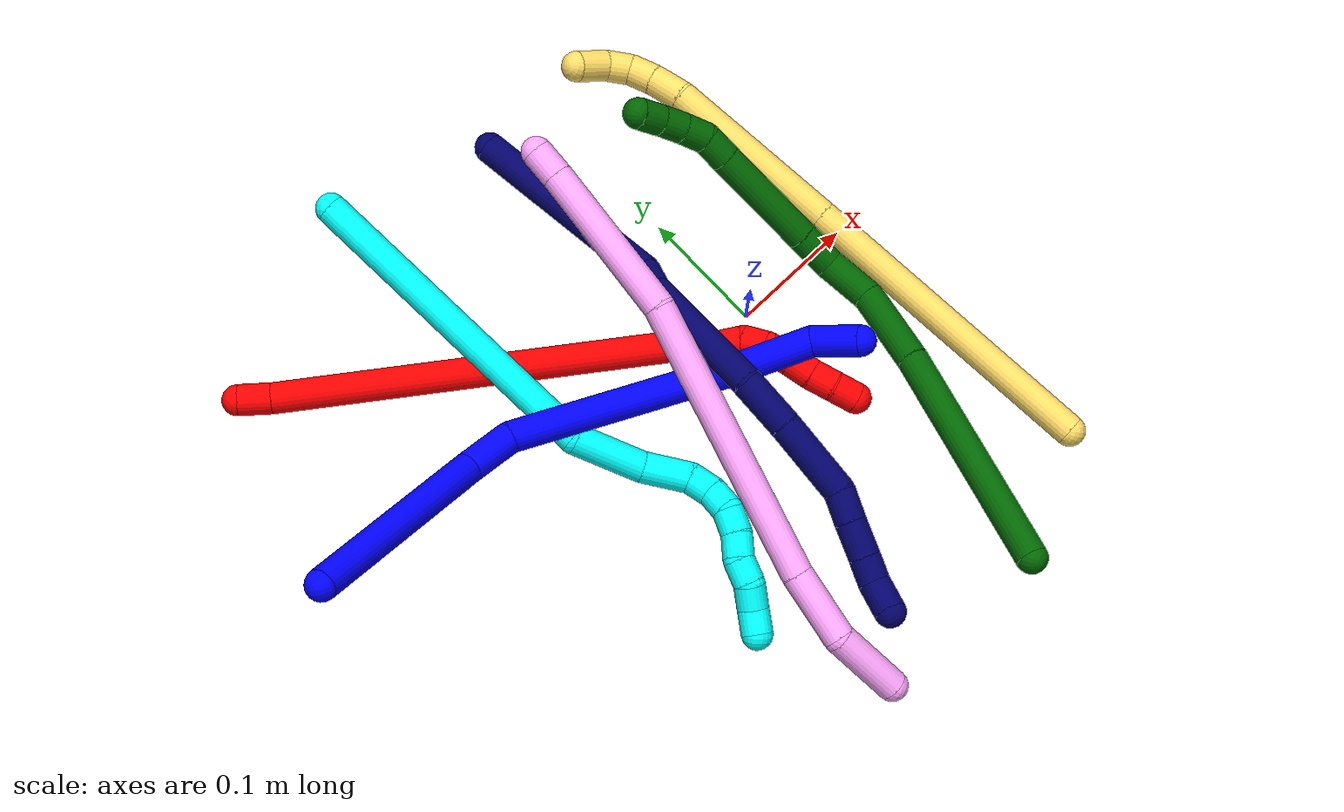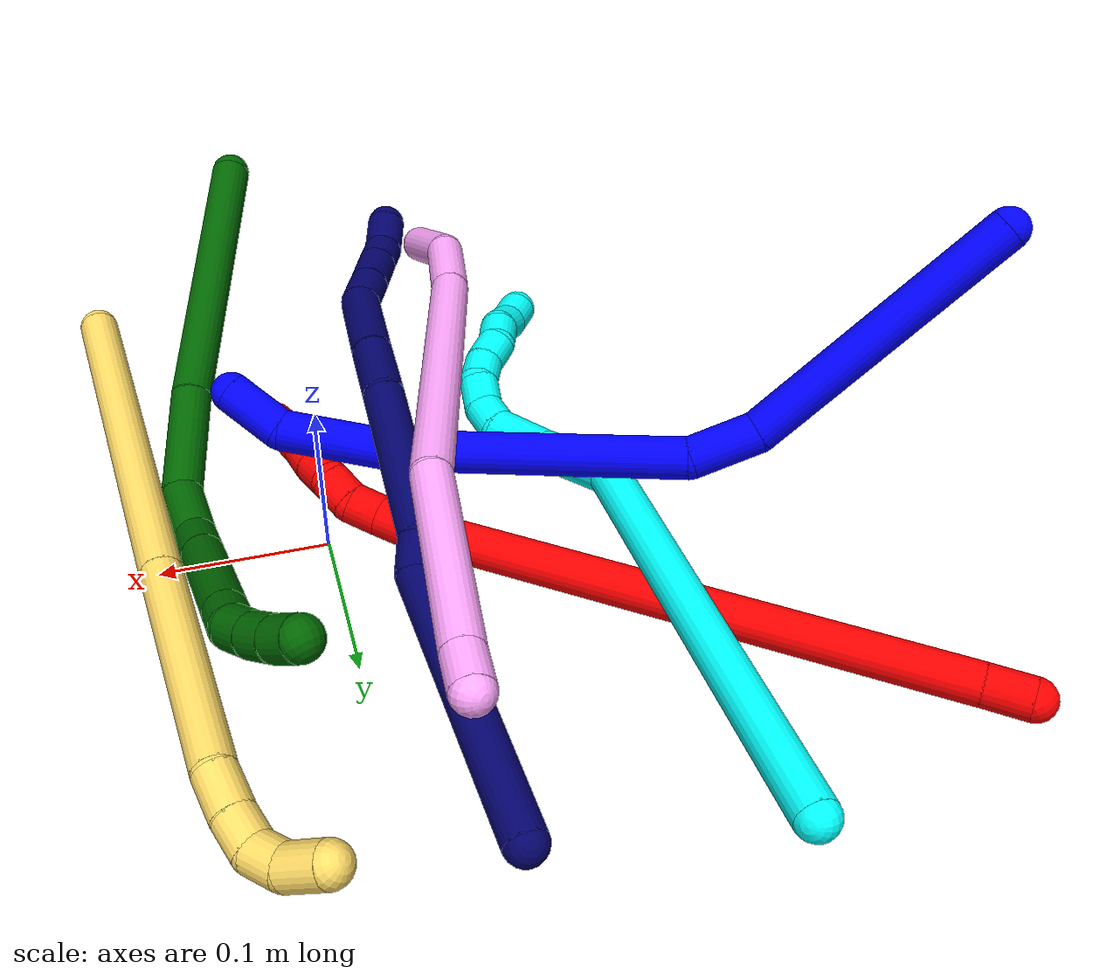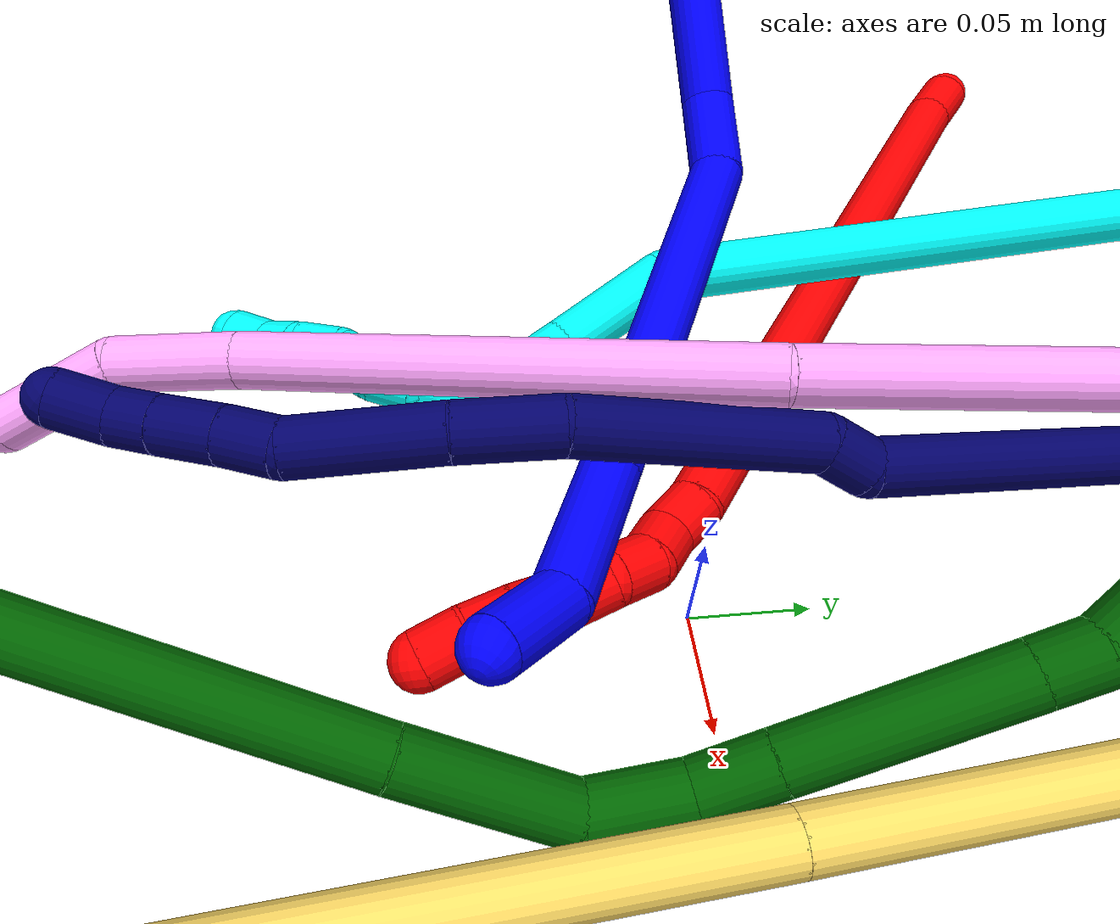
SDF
<sdf version="1.7">
 <world name="default">
  <plugin name="TubeGeneratorPlugin" filename="libtube_generator_plugin.so"/>
  <model name="photoneo_s_sensor">
   <static>1</static>
   <pose>0 0 2 1.57079 1.57079 3.14159</pose>
   <link name="link">
    <inertial><mass>0.1</mass></inertial>
    <sensor name="sensor" type="depth">
     <update_rate>30</update_rate>
     <camera>
      <horizontal_fov>1.22</horizontal_fov>
      <image><width>1920</width><height>1200</height><format>B8G8R8</format></image>
      <clip><near>0.1</near><far>4</far></clip>
      <depth_camera><output>points</output></depth_camera>
     </camera>
     <plugin name="camera_plugin" filename="libgazebo_ros_depth_camera.so">
      <baseline>0.2</baseline>
      <alwaysOn>1</alwaysOn>
      <updateRate>0.0</updateRate>
      <cameraName>camera_ir</cameraName>
      <imageTopicName>/camera/color/image_raw</imageTopicName>
      <cameraInfoTopicName>/camera/color/camera_info</cameraInfoTopicName>
      <depthImageTopicName>/camera/depth/image_raw</depthImageTopicName>
      <depthImageCameraInfoTopicName>/camera/depth/camera_info</depthImageCameraInfoTopicName>
      <pointCloudTopicName>/camera/depth/points</pointCloudTopicName>
      <frameName>fr_optical</frameName>
      <pointCloudCutoff>0.1</pointCloudCutoff>
      <pointCloudCutoffMax>2.0</pointCloudCutoffMax>
      <distortionK1>0</distortionK1>
      <distortionK2>0</distortionK2>
      <distortionK3>0</distortionK3>
      <distortionT1>0</distortionT1>
      <distortionT2>0</distortionT2>
      <CxPrime>0</CxPrime>
      <Cx>0</Cx>
      <Cy>0</Cy>
      <focalLength>0</focalLength>
      <hackBaseline>0</hackBaseline>
     </plugin>
    </sensor>
   </link>
  </model>
  <gravity>0 0 -9.8</gravity>
  <magnetic_field>6e-06 2.3e-05 -4.2e-05</magnetic_field>
  <atmosphere type="adiabatic"/>
  <physics name="default_physics" default="0" type="ode">
   <max_step_size>0.003</max_step_size>
   <real_time_factor>1</real_time_factor>
   <real_time_update_rate>1000</real_time_update_rate>
   <max_contacts>10000</max_contacts>
   <ode>
    <solver>
     <type>quick</type>
     <iters>100</iters>
     <sor>1.3</sor>
     <use_dynamic_moi_rescaling>0</use_dynamic_moi_rescaling>
    </solver>
    <constraints>
     <contact_max_correcting_vel>0</contact_max_correcting_vel>
     <contact_surface_layer>0.001</contact_surface_layer>
     <cfm>0</cfm>
     <erp>0.2</erp>
    </constraints>
   </ode>
  </physics>
  <scene><ambient>0.4 0.4 0.4 1</ambient><background>0.7 0.7 0.7 1</background><shadows>0</shadows></scene>
  <audio><device>default</device></audio>
  <spherical_coordinates>
   <surface_model>EARTH_WGS84</surface_model>
   <latitude_deg>0</latitude_deg>
   <longitude_deg>0</longitude_deg>
   <elevation>0</elevation>
   <heading_deg>0</heading_deg>
  </spherical_coordinates>
  <model name="bin">
   <static>1</static>
   <link name="bottom">
    <collision name="collision-bottom">
     <pose>0 0 -0.01 0 -0 0</pose>
     <geometry><box><size>0.8 0.6 0.02</size></box></geometry>
     <surface>
      <friction><ode><mu>100</mu><mu2>100</mu2></ode></friction>
      <contact><collide_bitmask>65535</collide_bitmask></contact>
     </surface>
    </collision>
   </link>
   <link name="west_wall">
    <collision name="collision-west_wall">
     <pose>-0.41 0 0.1 0 -0 0</pose>
     <geometry><box><size>0.02 0.6 0.2</size></box></geometry>
     <surface>
      <friction><ode><mu>100</mu><mu2>100</mu2></ode></friction>
      <contact><collide_bitmask>65535</collide_bitmask></contact>
     </surface>
    </collision>
   </link>
   <link name="east_wall">
    <collision name="collision-east_wall">
     <pose>0.41 0 0.1 0 -0 0</pose>
     <geometry><box><size>0.02 0.6 0.2</size></box></geometry>
     <surface>
      <friction><ode><mu>100</mu><mu2>100</mu2></ode></friction>
      <contact><collide_bitmask>65535</collide_bitmask></contact>
     </surface>
    </collision>
   </link>
   <link name="south_wall">
    <collision name="collision-south_wall">
     <pose>0 -0.31 0.1 0 -0 0</pose>
     <geometry><box><size>0.8 0.02 0.2</size></box></geometry>
     <surface>
      <friction><ode><mu>100</mu><mu2>100</mu2></ode></friction>
      <contact><collide_bitmask>65535</collide_bitmask></contact>
     </surface>
    </collision>
   </link>
   <link name="north_wall">
    <collision name="collision-north_wall">
     <pose>0 0.31 0.1 0 -0 0</pose>
     <geometry><box><size>0.8 0.02 0.2</size></box></geometry>
     <surface>
      <friction><ode><mu>100</mu><mu2>100</mu2></ode></friction>
      <contact><collide_bitmask>65535</collide_bitmask></contact>
     </surface>
    </collision>
   </link>
  </model>
  <model name="1">
   <static>0</static>
   <link name="1">
    <collision name="collision-cylinder-e_1_1_4">
     <pose>0.048441 -0.048336 -0.053985 2.41134 0.58927 1.34198</pose>
     <geometry><cylinder><radius>0.0125</radius><length>0.174324</length></cylinder></geometry>
     <surface>
      <friction><ode><mu>1.16</mu><mu2>1.16</mu2><slip1>0</slip1><slip2>0</slip2></ode></friction>
      <contact><ode><kp>1e+06</kp><kd>1</kd><max_vel>0</max_vel><min_depth>0.001</min_depth></ode></contact>
     </surface>
    </collision>
    <visual name="visual-cylinder-e_1_1_4">
     <pose>0.048441 -0.048336 -0.053985 2.41134 0.58927 1.34198</pose>
     <geometry><cylinder><radius>0.0125</radius><length>0.174324</length></cylinder></geometry>
     <material><ambient>0 0 1 1</ambient></material>
    </visual>
    <collision name="collision-cylinder-e_2_4_5">
     <pose>0.102335 -0.106719 -0.125175 2.61306 0.267165 0.921881</pose>
     <geometry><cylinder><radius>0.0125</radius><length>0.041315</length></cylinder></geometry>
     <surface>
      <friction><ode><mu>1.16</mu><mu2>1.16</mu2><slip1>0</slip1><slip2>0</slip2></ode></friction>
      <contact><ode><kp>1e+06</kp><kd>1</kd><max_vel>0</max_vel><min_depth>0.001</min_depth></ode></contact>
     </surface>
    </collision>
    <visual name="visual-cylinder-e_2_4_5">
     <pose>0.102335 -0.106719 -0.125175 2.61306 0.267165 0.921881</pose>
     <geometry><cylinder><radius>0.0125</radius><length>0.041315</length></cylinder></geometry>
     <material><ambient>0 0 1 1</ambient></material>
    </visual>
    <collision name="collision-cylinder-e_3_5_6">
     <pose>0.122094 -0.12617 -0.229341 3.03388 0.162125 1.96986</pose>
     <geometry><cylinder><radius>0.0125</radius><length>0.177257</length></cylinder></geometry>
     <surface>
      <friction><ode><mu>1.16</mu><mu2>1.16</mu2><slip1>0</slip1><slip2>0</slip2></ode></friction>
      <contact><ode><kp>1e+06</kp><kd>1</kd><max_vel>0</max_vel><min_depth>0.001</min_depth></ode></contact>
     </surface>
    </collision>
    <visual name="visual-cylinder-e_3_5_6">
     <pose>0.122094 -0.12617 -0.229341 3.03388 0.162125 1.96986</pose>
     <geometry><cylinder><radius>0.0125</radius><length>0.177257</length></cylinder></geometry>
     <material><ambient>0 0 1 1</ambient></material>
    </visual>
    <collision name="collision-cylinder-e_4_6_7">
     <pose>0.134451 -0.138268 -0.35035 3.06263 -0.05701 -1.25044</pose>
     <geometry><cylinder><radius>0.0125</radius><length>0.068424</length></cylinder></geometry>
     <surface>
      <friction><ode><mu>1.16</mu><mu2>1.16</mu2><slip1>0</slip1><slip2>0</slip2></ode></friction>
      <contact><ode><kp>1e+06</kp><kd>1</kd><max_vel>0</max_vel><min_depth>0.001</min_depth></ode></contact>
     </surface>
    </collision>
    <visual name="visual-cylinder-e_4_6_7">
     <pose>0.134451 -0.138268 -0.35035 3.06263 -0.05701 -1.25044</pose>
     <geometry><cylinder><radius>0.0125</radius><length>0.068424</length></cylinder></geometry>
     <material><ambient>0 0 1 1</ambient></material>
    </visual>
    <collision name="collision-cylinder-e_5_7_2">
     <pose>0.128191 -0.1343 -0.402037 -2.78041 -0.224788 1.10738</pose>
     <geometry><cylinder><radius>0.0125</radius><length>0.03868</length></cylinder></geometry>
     <surface>
      <friction><ode><mu>1.16</mu><mu2>1.16</mu2><slip1>0</slip1><slip2>0</slip2></ode></friction>
      <contact><ode><kp>1e+06</kp><kd>1</kd><max_vel>0</max_vel><min_depth>0.001</min_depth></ode></contact>
     </surface>
    </collision>
    <visual name="visual-cylinder-e_5_7_2">
     <pose>0.128191 -0.1343 -0.402037 -2.78041 -0.224788 1.10738</pose>
     <geometry><cylinder><radius>0.0125</radius><length>0.03868</length></cylinder></geometry>
     <material><ambient>0 0 1 1</ambient></material>
    </visual>
    <collision name="collision-sphere-2">
     <pose>0.12388 -0.127637 -0.419674 0 -0 0</pose>
     <geometry><sphere><radius>0.0125</radius></sphere></geometry>
     <surface>
      <friction><ode><mu>1.16</mu><mu2>1.16</mu2><slip1>0</slip1><slip2>0</slip2></ode></friction>
      <contact><ode><kp>1e+06</kp><kd>1</kd><max_vel>0</max_vel><min_depth>0.001</min_depth></ode></contact>
     </surface>
    </collision>
    <visual name="visual-sphere-2">
     <pose>0.12388 -0.127637 -0.419674 0 -0 0</pose>
     <geometry><sphere><radius>0.0125</radius></sphere></geometry>
     <material><ambient>0 0 1 1</ambient></material>
    </visual>
    <collision name="collision-sphere-7">
     <pose>0.132502 -0.140962 -0.3844 0 -0 0</pose>
     <geometry><sphere><radius>0.0125</radius></sphere></geometry>
     <surface>
      <friction><ode><mu>1.16</mu><mu2>1.16</mu2><slip1>0</slip1><slip2>0</slip2></ode></friction>
      <contact><ode><kp>1e+06</kp><kd>1</kd><max_vel>0</max_vel><min_depth>0.001</min_depth></ode></contact>
     </surface>
    </collision>
    <visual name="visual-sphere-7">
     <pose>0.132502 -0.140962 -0.3844 0 -0 0</pose>
     <geometry><sphere><radius>0.0125</radius></sphere></geometry>
     <material><ambient>0 0 1 1</ambient></material>
    </visual>
    <collision name="collision-sphere-6">
     <pose>0.1364 -0.135573 -0.3163 0 -0 0</pose>
     <geometry><sphere><radius>0.0125</radius></sphere></geometry>
     <surface>
      <friction><ode><mu>1.16</mu><mu2>1.16</mu2><slip1>0</slip1><slip2>0</slip2></ode></friction>
      <contact><ode><kp>1e+06</kp><kd>1</kd><max_vel>0</max_vel><min_depth>0.001</min_depth></ode></contact>
     </surface>
    </collision>
    <visual name="visual-sphere-6">
     <pose>0.1364 -0.135573 -0.3163 0 -0 0</pose>
     <geometry><sphere><radius>0.0125</radius></sphere></geometry>
     <material><ambient>0 0 1 1</ambient></material>
    </visual>
    <collision name="collision-sphere-5">
     <pose>0.107788 -0.116767 -0.142381 0 -0 0</pose>
     <geometry><sphere><radius>0.0125</radius></sphere></geometry>
     <surface>
      <friction><ode><mu>1.16</mu><mu2>1.16</mu2><slip1>0</slip1><slip2>0</slip2></ode></friction>
      <contact><ode><kp>1e+06</kp><kd>1</kd><max_vel>0</max_vel><min_depth>0.001</min_depth></ode></contact>
     </surface>
    </collision>
    <visual name="visual-sphere-5">
     <pose>0.107788 -0.116767 -0.142381 0 -0 0</pose>
     <geometry><sphere><radius>0.0125</radius></sphere></geometry>
     <material><ambient>0 0 1 1</ambient></material>
    </visual>
    <collision name="collision-sphere-1">
     <geometry><sphere><radius>0.0125</radius></sphere></geometry>
     <surface>
      <friction><ode><mu>1.16</mu><mu2>1.16</mu2><slip1>0</slip1><slip2>0</slip2></ode></friction>
      <contact><ode><kp>1e+06</kp><kd>1</kd><max_vel>0</max_vel><min_depth>0.001</min_depth></ode></contact>
     </surface>
    </collision>
    <visual name="visual-sphere-1">
     <geometry><sphere><radius>0.0125</radius></sphere></geometry>
     <material><ambient>0 0 1 1</ambient></material>
    </visual>
    <collision name="collision-sphere-4">
     <pose>0.096881 -0.096672 -0.107969 0 -0 0</pose>
     <geometry><sphere><radius>0.0125</radius></sphere></geometry>
     <surface>
      <friction><ode><mu>1.16</mu><mu2>1.16</mu2><slip1>0</slip1><slip2>0</slip2></ode></friction>
      <contact><ode><kp>1e+06</kp><kd>1</kd><max_vel>0</max_vel><min_depth>0.001</min_depth></ode></contact>
     </surface>
    </collision>
    <visual name="visual-sphere-4">
     <pose>0.096881 -0.096672 -0.107969 0 -0 0</pose>
     <geometry><sphere><radius>0.0125</radius></sphere></geometry>
     <material><ambient>0 0 1 1</ambient></material>
    </visual>
    <inertial>
     <pose>0.096945 -0.099711 -0.189516 0 -0 0</pose>
     <mass>0.5</mass>
     <inertia>
      <ixx>0.000705</ixx>
      <ixy>0</ixy>
      <ixz>0</ixz>
      <iyy>0.001026</iyy>
      <iyz>0</iyz>
      <izz>-5.4e-05</izz>
     </inertia>
    </inertial>
   </link>
   <pose>-0.380921 0.040521 0.184033 1.84651 1.34092 -1.80694</pose>
  </model>
  <model name="2">
   <static>0</static>
   <link name="2">
    <collision name="collision-cylinder-e_1_1_4">
     <pose>0.006738 -0.006937 -0.009121 2.49136 0.531512 1.35861</pose>
     <geometry><cylinder><radius>0.0125</radius><length>0.026587</length></cylinder></geometry>
     <surface>
      <friction><ode><mu>1.16</mu><mu2>1.16</mu2><slip1>0</slip1><slip2>0</slip2></ode></friction>
      <contact><ode><kp>1e+06</kp><kd>1</kd><max_vel>0</max_vel><min_depth>0.001</min_depth></ode></contact>
     </surface>
    </collision>
    <visual name="visual-cylinder-e_1_1_4">
     <pose>0.006738 -0.006937 -0.009121 2.49136 0.531512 1.35861</pose>
     <geometry><cylinder><radius>0.0125</radius><length>0.026587</length></cylinder></geometry>
     <material><ambient>1 0 0 1</ambient></material>
    </visual>
    <collision name="collision-cylinder-e_2_4_5">
     <pose>0.10514 -0.088674 -0.134784 2.57099 0.584716 1.59664</pose>
     <geometry><cylinder><radius>0.0125</radius><length>0.33214</length></cylinder></geometry>
     <surface>
      <friction><ode><mu>1.16</mu><mu2>1.16</mu2><slip1>0</slip1><slip2>0</slip2></ode></friction>
      <contact><ode><kp>1e+06</kp><kd>1</kd><max_vel>0</max_vel><min_depth>0.001</min_depth></ode></contact>
     </surface>
    </collision>
    <visual name="visual-cylinder-e_2_4_5">
     <pose>0.10514 -0.088674 -0.134784 2.57099 0.584716 1.59664</pose>
     <geometry><cylinder><radius>0.0125</radius><length>0.33214</length></cylinder></geometry>
     <material><ambient>1 0 0 1</ambient></material>
    </visual>
    <collision name="collision-cylinder-e_3_5_6">
     <pose>0.201883 -0.170031 -0.257575 2.332 0.510987 1.09494</pose>
     <geometry><cylinder><radius>0.0125</radius><length>0.020772</length></cylinder></geometry>
     <surface>
      <friction><ode><mu>1.16</mu><mu2>1.16</mu2><slip1>0</slip1><slip2>0</slip2></ode></friction>
      <contact><ode><kp>1e+06</kp><kd>1</kd><max_vel>0</max_vel><min_depth>0.001</min_depth></ode></contact>
     </surface>
    </collision>
    <visual name="visual-cylinder-e_3_5_6">
     <pose>0.201883 -0.170031 -0.257575 2.332 0.510987 1.09494</pose>
     <geometry><cylinder><radius>0.0125</radius><length>0.020772</length></cylinder></geometry>
     <material><ambient>1 0 0 1</ambient></material>
    </visual>
    <collision name="collision-cylinder-e_4_6_7">
     <pose>0.214603 -0.179924 -0.269675 2.62367 0.848381 2.08059</pose>
     <geometry><cylinder><radius>0.0125</radius><length>0.02037</length></cylinder></geometry>
     <surface>
      <friction><ode><mu>1.16</mu><mu2>1.16</mu2><slip1>0</slip1><slip2>0</slip2></ode></friction>
      <contact><ode><kp>1e+06</kp><kd>1</kd><max_vel>0</max_vel><min_depth>0.001</min_depth></ode></contact>
     </surface>
    </collision>
    <visual name="visual-cylinder-e_4_6_7">
     <pose>0.214603 -0.179924 -0.269675 2.62367 0.848381 2.08059</pose>
     <geometry><cylinder><radius>0.0125</radius><length>0.02037</length></cylinder></geometry>
     <material><ambient>1 0 0 1</ambient></material>
    </visual>
    <collision name="collision-cylinder-e_5_7_8">
     <pose>0.229305 -0.189886 -0.278191 1.9531 0.779598 1.09251</pose>
     <geometry><cylinder><radius>0.0125</radius><length>0.020089</length></cylinder></geometry>
     <surface>
      <friction><ode><mu>1.16</mu><mu2>1.16</mu2><slip1>0</slip1><slip2>0</slip2></ode></friction>
      <contact><ode><kp>1e+06</kp><kd>1</kd><max_vel>0</max_vel><min_depth>0.001</min_depth></ode></contact>
     </surface>
    </collision>
    <visual name="visual-cylinder-e_5_7_8">
     <pose>0.229305 -0.189886 -0.278191 1.9531 0.779598 1.09251</pose>
     <geometry><cylinder><radius>0.0125</radius><length>0.020089</length></cylinder></geometry>
     <material><ambient>1 0 0 1</ambient></material>
    </visual>
    <collision name="collision-cylinder-e_6_8_9">
     <pose>0.239333 -0.205536 -0.284036 1.9097 0.300767 0.421794</pose>
     <geometry><cylinder><radius>0.0125</radius><length>0.020031</length></cylinder></geometry>
     <surface>
      <friction><ode><mu>1.16</mu><mu2>1.16</mu2><slip1>0</slip1><slip2>0</slip2></ode></friction>
      <contact><ode><kp>1e+06</kp><kd>1</kd><max_vel>0</max_vel><min_depth>0.001</min_depth></ode></contact>
     </surface>
    </collision>
    <visual name="visual-cylinder-e_6_8_9">
     <pose>0.239333 -0.205536 -0.284036 1.9097 0.300767 0.421794</pose>
     <geometry><cylinder><radius>0.0125</radius><length>0.020031</length></cylinder></geometry>
     <material><ambient>1 0 0 1</ambient></material>
    </visual>
    <collision name="collision-cylinder-e_7_9_10">
     <pose>0.246002 -0.223632 -0.289204 1.78638 0.379137 0.468133</pose>
     <geometry><cylinder><radius>0.0125</radius><length>0.02</length></cylinder></geometry>
     <surface>
      <friction><ode><mu>1.16</mu><mu2>1.16</mu2><slip1>0</slip1><slip2>0</slip2></ode></friction>
      <contact><ode><kp>1e+06</kp><kd>1</kd><max_vel>0</max_vel><min_depth>0.001</min_depth></ode></contact>
     </surface>
    </collision>
    <visual name="visual-cylinder-e_7_9_10">
     <pose>0.246002 -0.223632 -0.289204 1.78638 0.379137 0.468133</pose>
     <geometry><cylinder><radius>0.0125</radius><length>0.02</length></cylinder></geometry>
     <material><ambient>1 0 0 1</ambient></material>
    </visual>
    <collision name="collision-cylinder-e_8_10_11">
     <pose>0.253755 -0.241416 -0.293985 1.88127 0.417043 0.564725</pose>
     <geometry><cylinder><radius>0.0125</radius><length>0.020007</length></cylinder></geometry>
     <surface>
      <friction><ode><mu>1.16</mu><mu2>1.16</mu2><slip1>0</slip1><slip2>0</slip2></ode></friction>
      <contact><ode><kp>1e+06</kp><kd>1</kd><max_vel>0</max_vel><min_depth>0.001</min_depth></ode></contact>
     </surface>
    </collision>
    <visual name="visual-cylinder-e_8_10_11">
     <pose>0.253755 -0.241416 -0.293985 1.88127 0.417043 0.564725</pose>
     <geometry><cylinder><radius>0.0125</radius><length>0.020007</length></cylinder></geometry>
     <material><ambient>1 0 0 1</ambient></material>
    </visual>
    <collision name="collision-cylinder-e_9_11_2">
     <pose>0.260708 -0.258996 -0.300376 1.95595 0.294256 0.43309</pose>
     <geometry><cylinder><radius>0.0125</radius><length>0.020004</length></cylinder></geometry>
     <surface>
      <friction><ode><mu>1.16</mu><mu2>1.16</mu2><slip1>0</slip1><slip2>0</slip2></ode></friction>
      <contact><ode><kp>1e+06</kp><kd>1</kd><max_vel>0</max_vel><min_depth>0.001</min_depth></ode></contact>
     </surface>
    </collision>
    <visual name="visual-cylinder-e_9_11_2">
     <pose>0.260708 -0.258996 -0.300376 1.95595 0.294256 0.43309</pose>
     <geometry><cylinder><radius>0.0125</radius><length>0.020004</length></cylinder></geometry>
     <material><ambient>1 0 0 1</ambient></material>
    </visual>
    <collision name="collision-sphere-2">
     <pose>0.263609 -0.267867 -0.303972 0 -0 0</pose>
     <geometry><sphere><radius>0.0125</radius></sphere></geometry>
     <surface>
      <friction><ode><mu>1.16</mu><mu2>1.16</mu2><slip1>0</slip1><slip2>0</slip2></ode></friction>
      <contact><ode><kp>1e+06</kp><kd>1</kd><max_vel>0</max_vel><min_depth>0.001</min_depth></ode></contact>
     </surface>
    </collision>
    <visual name="visual-sphere-2">
     <pose>0.263609 -0.267867 -0.303972 0 -0 0</pose>
     <geometry><sphere><radius>0.0125</radius></sphere></geometry>
     <material><ambient>1 0 0 1</ambient></material>
    </visual>
    <collision name="collision-sphere-11">
     <pose>0.257807 -0.250125 -0.29678 0 -0 0</pose>
     <geometry><sphere><radius>0.0125</radius></sphere></geometry>
     <surface>
      <friction><ode><mu>1.16</mu><mu2>1.16</mu2><slip1>0</slip1><slip2>0</slip2></ode></friction>
      <contact><ode><kp>1e+06</kp><kd>1</kd><max_vel>0</max_vel><min_depth>0.001</min_depth></ode></contact>
     </surface>
    </collision>
    <visual name="visual-sphere-11">
     <pose>0.257807 -0.250125 -0.29678 0 -0 0</pose>
     <geometry><sphere><radius>0.0125</radius></sphere></geometry>
     <material><ambient>1 0 0 1</ambient></material>
    </visual>
    <collision name="collision-sphere-10">
     <pose>0.249703 -0.232707 -0.291191 0 -0 0</pose>
     <geometry><sphere><radius>0.0125</radius></sphere></geometry>
     <surface>
      <friction><ode><mu>1.16</mu><mu2>1.16</mu2><slip1>0</slip1><slip2>0</slip2></ode></friction>
      <contact><ode><kp>1e+06</kp><kd>1</kd><max_vel>0</max_vel><min_depth>0.001</min_depth></ode></contact>
     </surface>
    </collision>
    <visual name="visual-sphere-10">
     <pose>0.249703 -0.232707 -0.291191 0 -0 0</pose>
     <geometry><sphere><radius>0.0125</radius></sphere></geometry>
     <material><ambient>1 0 0 1</ambient></material>
    </visual>
    <collision name="collision-sphere-9">
     <pose>0.242301 -0.214557 -0.287216 0 -0 0</pose>
     <geometry><sphere><radius>0.0125</radius></sphere></geometry>
     <surface>
      <friction><ode><mu>1.16</mu><mu2>1.16</mu2><slip1>0</slip1><slip2>0</slip2></ode></friction>
      <contact><ode><kp>1e+06</kp><kd>1</kd><max_vel>0</max_vel><min_depth>0.001</min_depth></ode></contact>
     </surface>
    </collision>
    <visual name="visual-sphere-9">
     <pose>0.242301 -0.214557 -0.287216 0 -0 0</pose>
     <geometry><sphere><radius>0.0125</radius></sphere></geometry>
     <material><ambient>1 0 0 1</ambient></material>
    </visual>
    <collision name="collision-sphere-4">
     <pose>0.013475 -0.013875 -0.018242 0 -0 0</pose>
     <geometry><sphere><radius>0.0125</radius></sphere></geometry>
     <surface>
      <friction><ode><mu>1.16</mu><mu2>1.16</mu2><slip1>0</slip1><slip2>0</slip2></ode></friction>
      <contact><ode><kp>1e+06</kp><kd>1</kd><max_vel>0</max_vel><min_depth>0.001</min_depth></ode></contact>
     </surface>
    </collision>
    <visual name="visual-sphere-4">
     <pose>0.013475 -0.013875 -0.018242 0 -0 0</pose>
     <geometry><sphere><radius>0.0125</radius></sphere></geometry>
     <material><ambient>1 0 0 1</ambient></material>
    </visual>
    <collision name="collision-sphere-1">
     <geometry><sphere><radius>0.0125</radius></sphere></geometry>
     <surface>
      <friction><ode><mu>1.16</mu><mu2>1.16</mu2><slip1>0</slip1><slip2>0</slip2></ode></friction>
      <contact><ode><kp>1e+06</kp><kd>1</kd><max_vel>0</max_vel><min_depth>0.001</min_depth></ode></contact>
     </surface>
    </collision>
    <visual name="visual-sphere-1">
     <geometry><sphere><radius>0.0125</radius></sphere></geometry>
     <material><ambient>1 0 0 1</ambient></material>
    </visual>
    <collision name="collision-sphere-8">
     <pose>0.236366 -0.196514 -0.280856 0 -0 0</pose>
     <geometry><sphere><radius>0.0125</radius></sphere></geometry>
     <surface>
      <friction><ode><mu>1.16</mu><mu2>1.16</mu2><slip1>0</slip1><slip2>0</slip2></ode></friction>
      <contact><ode><kp>1e+06</kp><kd>1</kd><max_vel>0</max_vel><min_depth>0.001</min_depth></ode></contact>
     </surface>
    </collision>
    <visual name="visual-sphere-8">
     <pose>0.236366 -0.196514 -0.280856 0 -0 0</pose>
     <geometry><sphere><radius>0.0125</radius></sphere></geometry>
     <material><ambient>1 0 0 1</ambient></material>
    </visual>
    <collision name="collision-sphere-5">
     <pose>0.196804 -0.163473 -0.251326 0 -0 0</pose>
     <geometry><sphere><radius>0.0125</radius></sphere></geometry>
     <surface>
      <friction><ode><mu>1.16</mu><mu2>1.16</mu2><slip1>0</slip1><slip2>0</slip2></ode></friction>
      <contact><ode><kp>1e+06</kp><kd>1</kd><max_vel>0</max_vel><min_depth>0.001</min_depth></ode></contact>
     </surface>
    </collision>
    <visual name="visual-sphere-5">
     <pose>0.196804 -0.163473 -0.251326 0 -0 0</pose>
     <geometry><sphere><radius>0.0125</radius></sphere></geometry>
     <material><ambient>1 0 0 1</ambient></material>
    </visual>
    <collision name="collision-sphere-6">
     <pose>0.206962 -0.17659 -0.263824 0 -0 0</pose>
     <geometry><sphere><radius>0.0125</radius></sphere></geometry>
     <surface>
      <friction><ode><mu>1.16</mu><mu2>1.16</mu2><slip1>0</slip1><slip2>0</slip2></ode></friction>
      <contact><ode><kp>1e+06</kp><kd>1</kd><max_vel>0</max_vel><min_depth>0.001</min_depth></ode></contact>
     </surface>
    </collision>
    <visual name="visual-sphere-6">
     <pose>0.206962 -0.17659 -0.263824 0 -0 0</pose>
     <geometry><sphere><radius>0.0125</radius></sphere></geometry>
     <material><ambient>1 0 0 1</ambient></material>
    </visual>
    <collision name="collision-sphere-7">
     <pose>0.222244 -0.183258 -0.275526 0 -0 0</pose>
     <geometry><sphere><radius>0.0125</radius></sphere></geometry>
     <surface>
      <friction><ode><mu>1.16</mu><mu2>1.16</mu2><slip1>0</slip1><slip2>0</slip2></ode></friction>
      <contact><ode><kp>1e+06</kp><kd>1</kd><max_vel>0</max_vel><min_depth>0.001</min_depth></ode></contact>
     </surface>
    </collision>
    <visual name="visual-sphere-7">
     <pose>0.222244 -0.183258 -0.275526 0 -0 0</pose>
     <geometry><sphere><radius>0.0125</radius></sphere></geometry>
     <material><ambient>1 0 0 1</ambient></material>
    </visual>
    <inertial>
     <pose>0.136556 -0.118497 -0.169612 0 -0 0</pose>
     <mass>0.5</mass>
     <inertia>
      <ixx>0.002524</ixx>
      <ixy>0</ixy>
      <ixz>0</ixz>
      <iyy>0.003525</iyy>
      <iyz>0</iyz>
      <izz>-0.000332</izz>
     </inertia>
    </inertial>
   </link>
   <pose>-0.337908 0.22176 0.0128 0.599448 -0.989627 -0.64606</pose>
  </model>
  <model name="3">
   <static>0</static>
   <link name="3">
    <collision name="collision-cylinder-e_1_1_4">
     <pose>0.033747 -0.100611 0.077132 0.916732 0.260166 0.12892</pose>
     <geometry><cylinder><radius>0.0125</radius><length>0.262381</length></cylinder></geometry>
     <surface>
      <friction><ode><mu>1.16</mu><mu2>1.16</mu2><slip1>0</slip1><slip2>0</slip2></ode></friction>
      <contact><ode><kp>1e+06</kp><kd>1</kd><max_vel>0</max_vel><min_depth>0.001</min_depth></ode></contact>
     </surface>
    </collision>
    <visual name="visual-cylinder-e_1_1_4">
     <pose>0.033747 -0.100611 0.077132 0.916732 0.260166 0.12892</pose>
     <geometry><cylinder><radius>0.0125</radius><length>0.262381</length></cylinder></geometry>
     <material><ambient>0.003922 1 0.996078 1</ambient></material>
    </visual>
    <collision name="collision-cylinder-e_2_4_5">
     <pose>0.06416 -0.228149 0.164715 1.20058 -0.114952 -0.078738</pose>
     <geometry><cylinder><radius>0.0125</radius><length>0.058152</length></cylinder></geometry>
     <surface>
      <friction><ode><mu>1.16</mu><mu2>1.16</mu2><slip1>0</slip1><slip2>0</slip2></ode></friction>
      <contact><ode><kp>1e+06</kp><kd>1</kd><max_vel>0</max_vel><min_depth>0.001</min_depth></ode></contact>
     </surface>
    </collision>
    <visual name="visual-cylinder-e_2_4_5">
     <pose>0.06416 -0.228149 0.164715 1.20058 -0.114952 -0.078738</pose>
     <geometry><cylinder><radius>0.0125</radius><length>0.058152</length></cylinder></geometry>
     <material><ambient>0.003922 1 0.996078 1</ambient></material>
    </visual>
    <collision name="collision-cylinder-e_3_5_6">
     <pose>0.061235 -0.274125 0.178157 1.41503 0.021247 0.018171</pose>
     <geometry><cylinder><radius>0.0125</radius><length>0.038572</length></cylinder></geometry>
     <surface>
      <friction><ode><mu>1.16</mu><mu2>1.16</mu2><slip1>0</slip1><slip2>0</slip2></ode></friction>
      <contact><ode><kp>1e+06</kp><kd>1</kd><max_vel>0</max_vel><min_depth>0.001</min_depth></ode></contact>
     </surface>
    </collision>
    <visual name="visual-cylinder-e_3_5_6">
     <pose>0.061235 -0.274125 0.178157 1.41503 0.021247 0.018171</pose>
     <geometry><cylinder><radius>0.0125</radius><length>0.038572</length></cylinder></geometry>
     <material><ambient>0.003922 1 0.996078 1</ambient></material>
    </visual>
    <collision name="collision-cylinder-e_4_6_7">
     <pose>0.064697 -0.301938 0.185486 1.11127 0.302616 0.188774</pose>
     <geometry><cylinder><radius>0.0125</radius><length>0.020489</length></cylinder></geometry>
     <surface>
      <friction><ode><mu>1.16</mu><mu2>1.16</mu2><slip1>0</slip1><slip2>0</slip2></ode></friction>
      <contact><ode><kp>1e+06</kp><kd>1</kd><max_vel>0</max_vel><min_depth>0.001</min_depth></ode></contact>
     </surface>
    </collision>
    <visual name="visual-cylinder-e_4_6_7">
     <pose>0.064697 -0.301938 0.185486 1.11127 0.302616 0.188774</pose>
     <geometry><cylinder><radius>0.0125</radius><length>0.020489</length></cylinder></geometry>
     <material><ambient>0.003922 1 0.996078 1</ambient></material>
    </visual>
    <collision name="collision-cylinder-e_5_7_8">
     <pose>0.074054 -0.316939 0.19475 0.902213 0.67047 0.334379</pose>
     <geometry><cylinder><radius>0.0125</radius><length>0.020288</length></cylinder></geometry>
     <surface>
      <friction><ode><mu>1.16</mu><mu2>1.16</mu2><slip1>0</slip1><slip2>0</slip2></ode></friction>
      <contact><ode><kp>1e+06</kp><kd>1</kd><max_vel>0</max_vel><min_depth>0.001</min_depth></ode></contact>
     </surface>
    </collision>
    <visual name="visual-cylinder-e_5_7_8">
     <pose>0.074054 -0.316939 0.19475 0.902213 0.67047 0.334379</pose>
     <geometry><cylinder><radius>0.0125</radius><length>0.020288</length></cylinder></geometry>
     <material><ambient>0.003922 1 0.996078 1</ambient></material>
    </visual>
    <collision name="collision-cylinder-e_6_8_9">
     <pose>0.084681 -0.32706 0.207819 0.445051 0.447035 0.10278</pose>
     <geometry><cylinder><radius>0.0125</radius><length>0.020008</length></cylinder></geometry>
     <surface>
      <friction><ode><mu>1.16</mu><mu2>1.16</mu2><slip1>0</slip1><slip2>0</slip2></ode></friction>
      <contact><ode><kp>1e+06</kp><kd>1</kd><max_vel>0</max_vel><min_depth>0.001</min_depth></ode></contact>
     </surface>
    </collision>
    <visual name="visual-cylinder-e_6_8_9">
     <pose>0.084681 -0.32706 0.207819 0.445051 0.447035 0.10278</pose>
     <geometry><cylinder><radius>0.0125</radius><length>0.020008</length></cylinder></geometry>
     <material><ambient>0.003922 1 0.996078 1</ambient></material>
    </visual>
    <collision name="collision-cylinder-e_7_9_10">
     <pose>0.094029 -0.332196 0.224569 0.144496 0.523715 0.038789</pose>
     <geometry><cylinder><radius>0.0125</radius><length>0.020089</length></cylinder></geometry>
     <surface>
      <friction><ode><mu>1.16</mu><mu2>1.16</mu2><slip1>0</slip1><slip2>0</slip2></ode></friction>
      <contact><ode><kp>1e+06</kp><kd>1</kd><max_vel>0</max_vel><min_depth>0.001</min_depth></ode></contact>
     </surface>
    </collision>
    <visual name="visual-cylinder-e_7_9_10">
     <pose>0.094029 -0.332196 0.224569 0.144496 0.523715 0.038789</pose>
     <geometry><cylinder><radius>0.0125</radius><length>0.020089</length></cylinder></geometry>
     <material><ambient>0.003922 1 0.996078 1</ambient></material>
    </visual>
    <collision name="collision-cylinder-e_8_10_11">
     <pose>0.102316 -0.338008 0.241467 0.502787 0.332094 0.08603</pose>
     <geometry><cylinder><radius>0.0125</radius><length>0.020018</length></cylinder></geometry>
     <surface>
      <friction><ode><mu>1.16</mu><mu2>1.16</mu2><slip1>0</slip1><slip2>0</slip2></ode></friction>
      <contact><ode><kp>1e+06</kp><kd>1</kd><max_vel>0</max_vel><min_depth>0.001</min_depth></ode></contact>
     </surface>
    </collision>
    <visual name="visual-cylinder-e_8_10_11">
     <pose>0.102316 -0.338008 0.241467 0.502787 0.332094 0.08603</pose>
     <geometry><cylinder><radius>0.0125</radius><length>0.020018</length></cylinder></geometry>
     <material><ambient>0.003922 1 0.996078 1</ambient></material>
    </visual>
    <collision name="collision-cylinder-e_9_11_12">
     <pose>0.105798 -0.34475 0.259515 0.220069 0.021925 0.002422</pose>
     <geometry><cylinder><radius>0.0125</radius><length>0.020001</length></cylinder></geometry>
     <surface>
      <friction><ode><mu>1.16</mu><mu2>1.16</mu2><slip1>0</slip1><slip2>0</slip2></ode></friction>
      <contact><ode><kp>1e+06</kp><kd>1</kd><max_vel>0</max_vel><min_depth>0.001</min_depth></ode></contact>
     </surface>
    </collision>
    <visual name="visual-cylinder-e_9_11_12">
     <pose>0.105798 -0.34475 0.259515 0.220069 0.021925 0.002422</pose>
     <geometry><cylinder><radius>0.0125</radius><length>0.020001</length></cylinder></geometry>
     <material><ambient>0.003922 1 0.996078 1</ambient></material>
    </visual>
    <collision name="collision-cylinder-e_10_12_2">
     <pose>0.109103 -0.349168 0.278519 0.237233 0.3137 0.037691</pose>
     <geometry><cylinder><radius>0.0125</radius><length>0.020003</length></cylinder></geometry>
     <surface>
      <friction><ode><mu>1.16</mu><mu2>1.16</mu2><slip1>0</slip1><slip2>0</slip2></ode></friction>
      <contact><ode><kp>1e+06</kp><kd>1</kd><max_vel>0</max_vel><min_depth>0.001</min_depth></ode></contact>
     </surface>
    </collision>
    <visual name="visual-cylinder-e_10_12_2">
     <pose>0.109103 -0.349168 0.278519 0.237233 0.3137 0.037691</pose>
     <geometry><cylinder><radius>0.0125</radius><length>0.020003</length></cylinder></geometry>
     <material><ambient>0.003922 1 0.996078 1</ambient></material>
    </visual>
    <collision name="collision-sphere-2">
     <pose>0.11219 -0.351404 0.287766 0 -0 0</pose>
     <geometry><sphere><radius>0.0125</radius></sphere></geometry>
     <surface>
      <friction><ode><mu>1.16</mu><mu2>1.16</mu2><slip1>0</slip1><slip2>0</slip2></ode></friction>
      <contact><ode><kp>1e+06</kp><kd>1</kd><max_vel>0</max_vel><min_depth>0.001</min_depth></ode></contact>
     </surface>
    </collision>
    <visual name="visual-sphere-2">
     <pose>0.11219 -0.351404 0.287766 0 -0 0</pose>
     <geometry><sphere><radius>0.0125</radius></sphere></geometry>
     <material><ambient>0.003922 1 0.996078 1</ambient></material>
    </visual>
    <collision name="collision-sphere-12">
     <pose>0.106017 -0.346932 0.269272 0 -0 0</pose>
     <geometry><sphere><radius>0.0125</radius></sphere></geometry>
     <surface>
      <friction><ode><mu>1.16</mu><mu2>1.16</mu2><slip1>0</slip1><slip2>0</slip2></ode></friction>
      <contact><ode><kp>1e+06</kp><kd>1</kd><max_vel>0</max_vel><min_depth>0.001</min_depth></ode></contact>
     </surface>
    </collision>
    <visual name="visual-sphere-12">
     <pose>0.106017 -0.346932 0.269272 0 -0 0</pose>
     <geometry><sphere><radius>0.0125</radius></sphere></geometry>
     <material><ambient>0.003922 1 0.996078 1</ambient></material>
    </visual>
    <collision name="collision-sphere-11">
     <pose>0.105579 -0.342567 0.249758 0 -0 0</pose>
     <geometry><sphere><radius>0.0125</radius></sphere></geometry>
     <surface>
      <friction><ode><mu>1.16</mu><mu2>1.16</mu2><slip1>0</slip1><slip2>0</slip2></ode></friction>
      <contact><ode><kp>1e+06</kp><kd>1</kd><max_vel>0</max_vel><min_depth>0.001</min_depth></ode></contact>
     </surface>
    </collision>
    <visual name="visual-sphere-11">
     <pose>0.105579 -0.342567 0.249758 0 -0 0</pose>
     <geometry><sphere><radius>0.0125</radius></sphere></geometry>
     <material><ambient>0.003922 1 0.996078 1</ambient></material>
    </visual>
    <collision name="collision-sphere-10">
     <pose>0.099053 -0.333448 0.233176 0 -0 0</pose>
     <geometry><sphere><radius>0.0125</radius></sphere></geometry>
     <surface>
      <friction><ode><mu>1.16</mu><mu2>1.16</mu2><slip1>0</slip1><slip2>0</slip2></ode></friction>
      <contact><ode><kp>1e+06</kp><kd>1</kd><max_vel>0</max_vel><min_depth>0.001</min_depth></ode></contact>
     </surface>
    </collision>
    <visual name="visual-sphere-10">
     <pose>0.099053 -0.333448 0.233176 0 -0 0</pose>
     <geometry><sphere><radius>0.0125</radius></sphere></geometry>
     <material><ambient>0.003922 1 0.996078 1</ambient></material>
    </visual>
    <collision name="collision-sphere-9">
     <pose>0.089006 -0.330943 0.215961 0 -0 0</pose>
     <geometry><sphere><radius>0.0125</radius></sphere></geometry>
     <surface>
      <friction><ode><mu>1.16</mu><mu2>1.16</mu2><slip1>0</slip1><slip2>0</slip2></ode></friction>
      <contact><ode><kp>1e+06</kp><kd>1</kd><max_vel>0</max_vel><min_depth>0.001</min_depth></ode></contact>
     </surface>
    </collision>
    <visual name="visual-sphere-9">
     <pose>0.089006 -0.330943 0.215961 0 -0 0</pose>
     <geometry><sphere><radius>0.0125</radius></sphere></geometry>
     <material><ambient>0.003922 1 0.996078 1</ambient></material>
    </visual>
    <collision name="collision-sphere-4">
     <pose>0.067495 -0.201222 0.154265 0 -0 0</pose>
     <geometry><sphere><radius>0.0125</radius></sphere></geometry>
     <surface>
      <friction><ode><mu>1.16</mu><mu2>1.16</mu2><slip1>0</slip1><slip2>0</slip2></ode></friction>
      <contact><ode><kp>1e+06</kp><kd>1</kd><max_vel>0</max_vel><min_depth>0.001</min_depth></ode></contact>
     </surface>
    </collision>
    <visual name="visual-sphere-4">
     <pose>0.067495 -0.201222 0.154265 0 -0 0</pose>
     <geometry><sphere><radius>0.0125</radius></sphere></geometry>
     <material><ambient>0.003922 1 0.996078 1</ambient></material>
    </visual>
    <collision name="collision-sphere-1">
     <geometry><sphere><radius>0.0125</radius></sphere></geometry>
     <surface>
      <friction><ode><mu>1.16</mu><mu2>1.16</mu2><slip1>0</slip1><slip2>0</slip2></ode></friction>
      <contact><ode><kp>1e+06</kp><kd>1</kd><max_vel>0</max_vel><min_depth>0.001</min_depth></ode></contact>
     </surface>
    </collision>
    <visual name="visual-sphere-1">
     <geometry><sphere><radius>0.0125</radius></sphere></geometry>
     <material><ambient>0.003922 1 0.996078 1</ambient></material>
    </visual>
    <collision name="collision-sphere-8">
     <pose>0.080357 -0.323176 0.199677 0 -0 0</pose>
     <geometry><sphere><radius>0.0125</radius></sphere></geometry>
     <surface>
      <friction><ode><mu>1.16</mu><mu2>1.16</mu2><slip1>0</slip1><slip2>0</slip2></ode></friction>
      <contact><ode><kp>1e+06</kp><kd>1</kd><max_vel>0</max_vel><min_depth>0.001</min_depth></ode></contact>
     </surface>
    </collision>
    <visual name="visual-sphere-8">
     <pose>0.080357 -0.323176 0.199677 0 -0 0</pose>
     <geometry><sphere><radius>0.0125</radius></sphere></geometry>
     <material><ambient>0.003922 1 0.996078 1</ambient></material>
    </visual>
    <collision name="collision-sphere-5">
     <pose>0.060825 -0.255077 0.175166 0 -0 0</pose>
     <geometry><sphere><radius>0.0125</radius></sphere></geometry>
     <surface>
      <friction><ode><mu>1.16</mu><mu2>1.16</mu2><slip1>0</slip1><slip2>0</slip2></ode></friction>
      <contact><ode><kp>1e+06</kp><kd>1</kd><max_vel>0</max_vel><min_depth>0.001</min_depth></ode></contact>
     </surface>
    </collision>
    <visual name="visual-sphere-5">
     <pose>0.060825 -0.255077 0.175166 0 -0 0</pose>
     <geometry><sphere><radius>0.0125</radius></sphere></geometry>
     <material><ambient>0.003922 1 0.996078 1</ambient></material>
    </visual>
    <collision name="collision-sphere-6">
     <pose>0.061644 -0.293173 0.181149 0 -0 0</pose>
     <geometry><sphere><radius>0.0125</radius></sphere></geometry>
     <surface>
      <friction><ode><mu>1.16</mu><mu2>1.16</mu2><slip1>0</slip1><slip2>0</slip2></ode></friction>
      <contact><ode><kp>1e+06</kp><kd>1</kd><max_vel>0</max_vel><min_depth>0.001</min_depth></ode></contact>
     </surface>
    </collision>
    <visual name="visual-sphere-6">
     <pose>0.061644 -0.293173 0.181149 0 -0 0</pose>
     <geometry><sphere><radius>0.0125</radius></sphere></geometry>
     <material><ambient>0.003922 1 0.996078 1</ambient></material>
    </visual>
    <collision name="collision-sphere-7">
     <pose>0.06775 -0.310702 0.189823 0 -0 0</pose>
     <geometry><sphere><radius>0.0125</radius></sphere></geometry>
     <surface>
      <friction><ode><mu>1.16</mu><mu2>1.16</mu2><slip1>0</slip1><slip2>0</slip2></ode></friction>
      <contact><ode><kp>1e+06</kp><kd>1</kd><max_vel>0</max_vel><min_depth>0.001</min_depth></ode></contact>
     </surface>
    </collision>
    <visual name="visual-sphere-7">
     <pose>0.06775 -0.310702 0.189823 0 -0 0</pose>
     <geometry><sphere><radius>0.0125</radius></sphere></geometry>
     <material><ambient>0.003922 1 0.996078 1</ambient></material>
    </visual>
    <inertial>
     <pose>0.055411 -0.193438 0.137409 0 -0 0</pose>
     <mass>0.5</mass>
     <inertia>
      <ixx>0.001683</ixx>
      <ixy>0</ixy>
      <ixz>0</ixz>
      <iyy>0.001131</iyy>
      <iyz>0</iyz>
      <izz>0.000821</izz>
     </inertia>
    </inertial>
   </link>
   <pose>-0.184164 0.278473 0.043296 3.03582 -1.14567 -2.2869</pose>
  </model>
  <model name="4">
   <static>0</static>
   <link name="4">
    <collision name="collision-cylinder-e_1_1_4">
     <pose>0.005569 0.006419 0.028941 -0.218258 0.185705 -0.020405</pose>
     <geometry><cylinder><radius>0.0125</radius><length>0.060326</length></cylinder></geometry>
     <surface>
      <friction><ode><mu>1.16</mu><mu2>1.16</mu2><slip1>0</slip1><slip2>0</slip2></ode></friction>
      <contact><ode><kp>1e+06</kp><kd>1</kd><max_vel>0</max_vel><min_depth>0.001</min_depth></ode></contact>
     </surface>
    </collision>
    <visual name="visual-cylinder-e_1_1_4">
     <pose>0.005569 0.006419 0.028941 -0.218258 0.185705 -0.020405</pose>
     <geometry><cylinder><radius>0.0125</radius><length>0.060326</length></cylinder></geometry>
     <material><ambient>1 0.65098 0.996078 1</ambient></material>
    </visual>
    <collision name="collision-cylinder-e_2_4_5">
     <pose>0.010929 0.029174 0.081365 -0.607814 -0.007329 0.002299</pose>
     <geometry><cylinder><radius>0.0125</radius><length>0.057214</length></cylinder></geometry>
     <surface>
      <friction><ode><mu>1.16</mu><mu2>1.16</mu2><slip1>0</slip1><slip2>0</slip2></ode></friction>
      <contact><ode><kp>1e+06</kp><kd>1</kd><max_vel>0</max_vel><min_depth>0.001</min_depth></ode></contact>
     </surface>
    </collision>
    <visual name="visual-cylinder-e_2_4_5">
     <pose>0.010929 0.029174 0.081365 -0.607814 -0.007329 0.002299</pose>
     <geometry><cylinder><radius>0.0125</radius><length>0.057214</length></cylinder></geometry>
     <material><ambient>1 0.65098 0.996078 1</ambient></material>
    </visual>
    <collision name="collision-cylinder-e_3_5_6">
     <pose>0.017218 0.118513 0.192195 -0.696177 0.057023 -0.020696</pose>
     <geometry><cylinder><radius>0.0125</radius><length>0.228046</length></cylinder></geometry>
     <surface>
      <friction><ode><mu>1.16</mu><mu2>1.16</mu2><slip1>0</slip1><slip2>0</slip2></ode></friction>
      <contact><ode><kp>1e+06</kp><kd>1</kd><max_vel>0</max_vel><min_depth>0.001</min_depth></ode></contact>
     </surface>
    </collision>
    <visual name="visual-cylinder-e_3_5_6">
     <pose>0.017218 0.118513 0.192195 -0.696177 0.057023 -0.020696</pose>
     <geometry><cylinder><radius>0.0125</radius><length>0.228046</length></cylinder></geometry>
     <material><ambient>1 0.65098 0.996078 1</ambient></material>
    </visual>
    <collision name="collision-cylinder-e_4_6_7">
     <pose>0.014085 0.227735 0.33221 -0.602419 -0.149552 0.046538</pose>
     <geometry><cylinder><radius>0.0125</radius><length>0.12928</length></cylinder></geometry>
     <surface>
      <friction><ode><mu>1.16</mu><mu2>1.16</mu2><slip1>0</slip1><slip2>0</slip2></ode></friction>
      <contact><ode><kp>1e+06</kp><kd>1</kd><max_vel>0</max_vel><min_depth>0.001</min_depth></ode></contact>
     </surface>
    </collision>
    <visual name="visual-cylinder-e_4_6_7">
     <pose>0.014085 0.227735 0.33221 -0.602419 -0.149552 0.046538</pose>
     <geometry><cylinder><radius>0.0125</radius><length>0.12928</length></cylinder></geometry>
     <material><ambient>1 0.65098 0.996078 1</ambient></material>
    </visual>
    <collision name="collision-cylinder-e_5_7_2">
     <pose>0.002759 0.270447 0.395502 -0.548554 -0.135265 0.038113</pose>
     <geometry><cylinder><radius>0.0125</radius><length>0.025134</length></cylinder></geometry>
     <surface>
      <friction><ode><mu>1.16</mu><mu2>1.16</mu2><slip1>0</slip1><slip2>0</slip2></ode></friction>
      <contact><ode><kp>1e+06</kp><kd>1</kd><max_vel>0</max_vel><min_depth>0.001</min_depth></ode></contact>
     </surface>
    </collision>
    <visual name="visual-cylinder-e_5_7_2">
     <pose>0.002759 0.270447 0.395502 -0.548554 -0.135265 0.038113</pose>
     <geometry><cylinder><radius>0.0125</radius><length>0.025134</length></cylinder></geometry>
     <material><ambient>1 0.65098 0.996078 1</ambient></material>
    </visual>
    <collision name="collision-sphere-2">
     <pose>0.001065 0.27694 0.406127 0 -0 0</pose>
     <geometry><sphere><radius>0.0125</radius></sphere></geometry>
     <surface>
      <friction><ode><mu>1.16</mu><mu2>1.16</mu2><slip1>0</slip1><slip2>0</slip2></ode></friction>
      <contact><ode><kp>1e+06</kp><kd>1</kd><max_vel>0</max_vel><min_depth>0.001</min_depth></ode></contact>
     </surface>
    </collision>
    <visual name="visual-sphere-2">
     <pose>0.001065 0.27694 0.406127 0 -0 0</pose>
     <geometry><sphere><radius>0.0125</radius></sphere></geometry>
     <material><ambient>1 0.65098 0.996078 1</ambient></material>
    </visual>
    <collision name="collision-sphere-7">
     <pose>0.004454 0.263953 0.384877 0 -0 0</pose>
     <geometry><sphere><radius>0.0125</radius></sphere></geometry>
     <surface>
      <friction><ode><mu>1.16</mu><mu2>1.16</mu2><slip1>0</slip1><slip2>0</slip2></ode></friction>
      <contact><ode><kp>1e+06</kp><kd>1</kd><max_vel>0</max_vel><min_depth>0.001</min_depth></ode></contact>
     </surface>
    </collision>
    <visual name="visual-sphere-7">
     <pose>0.004454 0.263953 0.384877 0 -0 0</pose>
     <geometry><sphere><radius>0.0125</radius></sphere></geometry>
     <material><ambient>1 0.65098 0.996078 1</ambient></material>
    </visual>
    <collision name="collision-sphere-6">
     <pose>0.023716 0.191516 0.279543 0 -0 0</pose>
     <geometry><sphere><radius>0.0125</radius></sphere></geometry>
     <surface>
      <friction><ode><mu>1.16</mu><mu2>1.16</mu2><slip1>0</slip1><slip2>0</slip2></ode></friction>
      <contact><ode><kp>1e+06</kp><kd>1</kd><max_vel>0</max_vel><min_depth>0.001</min_depth></ode></contact>
     </surface>
    </collision>
    <visual name="visual-sphere-6">
     <pose>0.023716 0.191516 0.279543 0 -0 0</pose>
     <geometry><sphere><radius>0.0125</radius></sphere></geometry>
     <material><ambient>1 0.65098 0.996078 1</ambient></material>
    </visual>
    <collision name="collision-sphere-5">
     <pose>0.010719 0.04551 0.104848 0 -0 0</pose>
     <geometry><sphere><radius>0.0125</radius></sphere></geometry>
     <surface>
      <friction><ode><mu>1.16</mu><mu2>1.16</mu2><slip1>0</slip1><slip2>0</slip2></ode></friction>
      <contact><ode><kp>1e+06</kp><kd>1</kd><max_vel>0</max_vel><min_depth>0.001</min_depth></ode></contact>
     </surface>
    </collision>
    <visual name="visual-sphere-5">
     <pose>0.010719 0.04551 0.104848 0 -0 0</pose>
     <geometry><sphere><radius>0.0125</radius></sphere></geometry>
     <material><ambient>1 0.65098 0.996078 1</ambient></material>
    </visual>
    <collision name="collision-sphere-1">
     <geometry><sphere><radius>0.0125</radius></sphere></geometry>
     <surface>
      <friction><ode><mu>1.16</mu><mu2>1.16</mu2><slip1>0</slip1><slip2>0</slip2></ode></friction>
      <contact><ode><kp>1e+06</kp><kd>1</kd><max_vel>0</max_vel><min_depth>0.001</min_depth></ode></contact>
     </surface>
    </collision>
    <visual name="visual-sphere-1">
     <geometry><sphere><radius>0.0125</radius></sphere></geometry>
     <material><ambient>1 0.65098 0.996078 1</ambient></material>
    </visual>
    <collision name="collision-sphere-4">
     <pose>0.011139 0.012838 0.057882 0 -0 0</pose>
     <geometry><sphere><radius>0.0125</radius></sphere></geometry>
     <surface>
      <friction><ode><mu>1.16</mu><mu2>1.16</mu2><slip1>0</slip1><slip2>0</slip2></ode></friction>
      <contact><ode><kp>1e+06</kp><kd>1</kd><max_vel>0</max_vel><min_depth>0.001</min_depth></ode></contact>
     </surface>
    </collision>
    <visual name="visual-sphere-4">
     <pose>0.011139 0.012838 0.057882 0 -0 0</pose>
     <geometry><sphere><radius>0.0125</radius></sphere></geometry>
     <material><ambient>1 0.65098 0.996078 1</ambient></material>
    </visual>
    <inertial>
     <pose>0.013556 0.130644 0.206238 0 -0 0</pose>
     <mass>0.5</mass>
     <inertia>
      <ixx>0.001206</ixx>
      <ixy>0</ixy>
      <ixz>0</ixz>
      <iyy>0.000965</iyy>
      <iyz>0</iyz>
      <izz>-0.000759</izz>
     </inertia>
    </inertial>
   </link>
   <pose>-0.118704 -0.286961 0.012603 -0.65302 -1.13999 -0.4498</pose>
  </model>
  <model name="5">
   <static>0</static>
   <link name="5">
    <collision name="collision-cylinder-e_1_1_4">
     <pose>-0.008047 0.115718 -0.054569 -2.01144 -0.062818 0.099027</pose>
     <geometry><cylinder><radius>0.0125</radius><length>0.256384</length></cylinder></geometry>
     <surface>
      <friction><ode><mu>1.16</mu><mu2>1.16</mu2><slip1>0</slip1><slip2>0</slip2></ode></friction>
      <contact><ode><kp>1e+06</kp><kd>1</kd><max_vel>0</max_vel><min_depth>0.001</min_depth></ode></contact>
     </surface>
    </collision>
    <visual name="visual-cylinder-e_1_1_4">
     <pose>-0.008047 0.115718 -0.054569 -2.01144 -0.062818 0.099027</pose>
     <geometry><cylinder><radius>0.0125</radius><length>0.256384</length></cylinder></geometry>
     <material><ambient>1 0.858824 0.4 1</ambient></material>
    </visual>
    <collision name="collision-cylinder-e_2_4_5">
     <pose>-0.020072 0.298281 -0.140873 -2.01404 -0.053698 0.084904</pose>
     <geometry><cylinder><radius>0.0125</radius><length>0.148205</length></cylinder></geometry>
     <surface>
      <friction><ode><mu>1.16</mu><mu2>1.16</mu2><slip1>0</slip1><slip2>0</slip2></ode></friction>
      <contact><ode><kp>1e+06</kp><kd>1</kd><max_vel>0</max_vel><min_depth>0.001</min_depth></ode></contact>
     </surface>
    </collision>
    <visual name="visual-cylinder-e_2_4_5">
     <pose>-0.020072 0.298281 -0.140873 -2.01404 -0.053698 0.084904</pose>
     <geometry><cylinder><radius>0.0125</radius><length>0.148205</length></cylinder></geometry>
     <material><ambient>1 0.858824 0.4 1</ambient></material>
    </visual>
    <collision name="collision-cylinder-e_3_5_6">
     <pose>-0.022135 0.377517 -0.177718 -1.96195 0.141898 -0.211576</pose>
     <geometry><cylinder><radius>0.0125</radius><length>0.027079</length></cylinder></geometry>
     <surface>
      <friction><ode><mu>1.16</mu><mu2>1.16</mu2><slip1>0</slip1><slip2>0</slip2></ode></friction>
      <contact><ode><kp>1e+06</kp><kd>1</kd><max_vel>0</max_vel><min_depth>0.001</min_depth></ode></contact>
     </surface>
    </collision>
    <visual name="visual-cylinder-e_3_5_6">
     <pose>-0.022135 0.377517 -0.177718 -1.96195 0.141898 -0.211576</pose>
     <geometry><cylinder><radius>0.0125</radius><length>0.027079</length></cylinder></geometry>
     <material><ambient>1 0.858824 0.4 1</ambient></material>
    </visual>
    <collision name="collision-cylinder-e_4_6_7">
     <pose>-0.017659 0.399258 -0.187482 -2.03265 0.240441 -0.385305</pose>
     <geometry><cylinder><radius>0.0125</radius><length>0.021508</length></cylinder></geometry>
     <surface>
      <friction><ode><mu>1.16</mu><mu2>1.16</mu2><slip1>0</slip1><slip2>0</slip2></ode></friction>
      <contact><ode><kp>1e+06</kp><kd>1</kd><max_vel>0</max_vel><min_depth>0.001</min_depth></ode></contact>
     </surface>
    </collision>
    <visual name="visual-cylinder-e_4_6_7">
     <pose>-0.017659 0.399258 -0.187482 -2.03265 0.240441 -0.385305</pose>
     <geometry><cylinder><radius>0.0125</radius><length>0.021508</length></cylinder></geometry>
     <material><ambient>1 0.858824 0.4 1</ambient></material>
    </visual>
    <collision name="collision-cylinder-e_5_7_8">
     <pose>-0.011861 0.414171 -0.200111 -2.5325 0.321361 -0.952153</pose>
     <geometry><cylinder><radius>0.0125</radius><length>0.020497</length></cylinder></geometry>
     <surface>
      <friction><ode><mu>1.16</mu><mu2>1.16</mu2><slip1>0</slip1><slip2>0</slip2></ode></friction>
      <contact><ode><kp>1e+06</kp><kd>1</kd><max_vel>0</max_vel><min_depth>0.001</min_depth></ode></contact>
     </surface>
    </collision>
    <visual name="visual-cylinder-e_5_7_8">
     <pose>-0.011861 0.414171 -0.200111 -2.5325 0.321361 -0.952153</pose>
     <geometry><cylinder><radius>0.0125</radius><length>0.020497</length></cylinder></geometry>
     <material><ambient>1 0.858824 0.4 1</ambient></material>
    </visual>
    <collision name="collision-cylinder-e_6_8_2">
     <pose>-0.005164 0.421735 -0.220629 -2.98344 0.266007 -2.07216</pose>
     <geometry><cylinder><radius>0.0125</radius><length>0.026328</length></cylinder></geometry>
     <surface>
      <friction><ode><mu>1.16</mu><mu2>1.16</mu2><slip1>0</slip1><slip2>0</slip2></ode></friction>
      <contact><ode><kp>1e+06</kp><kd>1</kd><max_vel>0</max_vel><min_depth>0.001</min_depth></ode></contact>
     </surface>
    </collision>
    <visual name="visual-cylinder-e_6_8_2">
     <pose>-0.005164 0.421735 -0.220629 -2.98344 0.266007 -2.07216</pose>
     <geometry><cylinder><radius>0.0125</radius><length>0.026328</length></cylinder></geometry>
     <material><ambient>1 0.858824 0.4 1</ambient></material>
    </visual>
    <collision name="collision-sphere-2">
     <pose>-0.001703 0.423735 -0.233171 0 -0 0</pose>
     <geometry><sphere><radius>0.0125</radius></sphere></geometry>
     <surface>
      <friction><ode><mu>1.16</mu><mu2>1.16</mu2><slip1>0</slip1><slip2>0</slip2></ode></friction>
      <contact><ode><kp>1e+06</kp><kd>1</kd><max_vel>0</max_vel><min_depth>0.001</min_depth></ode></contact>
     </surface>
    </collision>
    <visual name="visual-sphere-2">
     <pose>-0.001703 0.423735 -0.233171 0 -0 0</pose>
     <geometry><sphere><radius>0.0125</radius></sphere></geometry>
     <material><ambient>1 0.858824 0.4 1</ambient></material>
    </visual>
    <collision name="collision-sphere-4">
     <pose>-0.016095 0.231436 -0.109138 0 -0 0</pose>
     <geometry><sphere><radius>0.0125</radius></sphere></geometry>
     <surface>
      <friction><ode><mu>1.16</mu><mu2>1.16</mu2><slip1>0</slip1><slip2>0</slip2></ode></friction>
      <contact><ode><kp>1e+06</kp><kd>1</kd><max_vel>0</max_vel><min_depth>0.001</min_depth></ode></contact>
     </surface>
    </collision>
    <visual name="visual-sphere-4">
     <pose>-0.016095 0.231436 -0.109138 0 -0 0</pose>
     <geometry><sphere><radius>0.0125</radius></sphere></geometry>
     <material><ambient>1 0.858824 0.4 1</ambient></material>
    </visual>
    <collision name="collision-sphere-1">
     <geometry><sphere><radius>0.0125</radius></sphere></geometry>
     <surface>
      <friction><ode><mu>1.16</mu><mu2>1.16</mu2><slip1>0</slip1><slip2>0</slip2></ode></friction>
      <contact><ode><kp>1e+06</kp><kd>1</kd><max_vel>0</max_vel><min_depth>0.001</min_depth></ode></contact>
     </surface>
    </collision>
    <visual name="visual-sphere-1">
     <geometry><sphere><radius>0.0125</radius></sphere></geometry>
     <material><ambient>1 0.858824 0.4 1</ambient></material>
    </visual>
    <collision name="collision-sphere-8">
     <pose>-0.008624 0.419734 -0.208086 0 -0 0</pose>
     <geometry><sphere><radius>0.0125</radius></sphere></geometry>
     <surface>
      <friction><ode><mu>1.16</mu><mu2>1.16</mu2><slip1>0</slip1><slip2>0</slip2></ode></friction>
      <contact><ode><kp>1e+06</kp><kd>1</kd><max_vel>0</max_vel><min_depth>0.001</min_depth></ode></contact>
     </surface>
    </collision>
    <visual name="visual-sphere-8">
     <pose>-0.008624 0.419734 -0.208086 0 -0 0</pose>
     <geometry><sphere><radius>0.0125</radius></sphere></geometry>
     <material><ambient>1 0.858824 0.4 1</ambient></material>
    </visual>
    <collision name="collision-sphere-5">
     <pose>-0.024049 0.365125 -0.172607 0 -0 0</pose>
     <geometry><sphere><radius>0.0125</radius></sphere></geometry>
     <surface>
      <friction><ode><mu>1.16</mu><mu2>1.16</mu2><slip1>0</slip1><slip2>0</slip2></ode></friction>
      <contact><ode><kp>1e+06</kp><kd>1</kd><max_vel>0</max_vel><min_depth>0.001</min_depth></ode></contact>
     </surface>
    </collision>
    <visual name="visual-sphere-5">
     <pose>-0.024049 0.365125 -0.172607 0 -0 0</pose>
     <geometry><sphere><radius>0.0125</radius></sphere></geometry>
     <material><ambient>1 0.858824 0.4 1</ambient></material>
    </visual>
    <collision name="collision-sphere-6">
     <pose>-0.02022 0.389908 -0.182828 0 -0 0</pose>
     <geometry><sphere><radius>0.0125</radius></sphere></geometry>
     <surface>
      <friction><ode><mu>1.16</mu><mu2>1.16</mu2><slip1>0</slip1><slip2>0</slip2></ode></friction>
      <contact><ode><kp>1e+06</kp><kd>1</kd><max_vel>0</max_vel><min_depth>0.001</min_depth></ode></contact>
     </surface>
    </collision>
    <visual name="visual-sphere-6">
     <pose>-0.02022 0.389908 -0.182828 0 -0 0</pose>
     <geometry><sphere><radius>0.0125</radius></sphere></geometry>
     <material><ambient>1 0.858824 0.4 1</ambient></material>
    </visual>
    <collision name="collision-sphere-7">
     <pose>-0.015098 0.408608 -0.192136 0 -0 0</pose>
     <geometry><sphere><radius>0.0125</radius></sphere></geometry>
     <surface>
      <friction><ode><mu>1.16</mu><mu2>1.16</mu2><slip1>0</slip1><slip2>0</slip2></ode></friction>
      <contact><ode><kp>1e+06</kp><kd>1</kd><max_vel>0</max_vel><min_depth>0.001</min_depth></ode></contact>
     </surface>
    </collision>
    <visual name="visual-sphere-7">
     <pose>-0.015098 0.408608 -0.192136 0 -0 0</pose>
     <geometry><sphere><radius>0.0125</radius></sphere></geometry>
     <material><ambient>1 0.858824 0.4 1</ambient></material>
    </visual>
    <inertial>
     <pose>-0.012793 0.224555 -0.107248 0 -0 0</pose>
     <mass>0.5</mass>
     <inertia>
      <ixx>0.001843</ixx>
      <ixy>0</ixy>
      <ixz>0</ixz>
      <iyy>-0.000519</iyy>
      <iyz>0</iyz>
      <izz>-0.001448</izz>
     </inertia>
    </inertial>
   </link>
   <pose>0.120012 -0.239963 0.012281 -2.67697 0.627054 -2.98954</pose>
  </model>
  <model name="6">
   <static>0</static>
   <link name="6">
    <collision name="collision-cylinder-e_1_1_4">
     <pose>0.041866 0.035439 -0.075667 -2.70358 0.4645 -1.63152</pose>
     <geometry><cylinder><radius>0.0125</radius><length>0.186913</length></cylinder></geometry>
     <surface>
      <friction><ode><mu>1.16</mu><mu2>1.16</mu2><slip1>0</slip1><slip2>0</slip2></ode></friction>
      <contact><ode><kp>1e+06</kp><kd>1</kd><max_vel>0</max_vel><min_depth>0.001</min_depth></ode></contact>
     </surface>
    </collision>
    <visual name="visual-cylinder-e_1_1_4">
     <pose>0.041866 0.035439 -0.075667 -2.70358 0.4645 -1.63152</pose>
     <geometry><cylinder><radius>0.0125</radius><length>0.186913</length></cylinder></geometry>
     <material><ambient>0 0.392157 0.003922 1</ambient></material>
    </visual>
    <collision name="collision-cylinder-e_2_4_5">
     <pose>0.098006 0.081808 -0.18071 -2.78535 0.427305 -1.75633</pose>
     <geometry><cylinder><radius>0.0125</radius><length>0.068882</length></cylinder></geometry>
     <surface>
      <friction><ode><mu>1.16</mu><mu2>1.16</mu2><slip1>0</slip1><slip2>0</slip2></ode></friction>
      <contact><ode><kp>1e+06</kp><kd>1</kd><max_vel>0</max_vel><min_depth>0.001</min_depth></ode></contact>
     </surface>
    </collision>
    <visual name="visual-cylinder-e_2_4_5">
     <pose>0.098006 0.081808 -0.18071 -2.78535 0.427305 -1.75633</pose>
     <geometry><cylinder><radius>0.0125</radius><length>0.068882</length></cylinder></geometry>
     <material><ambient>0 0.392157 0.003922 1</ambient></material>
    </visual>
    <collision name="collision-cylinder-e_3_5_6">
     <pose>0.112317 0.104453 -0.226555 -2.52336 0.001906 -0.005969</pose>
     <geometry><cylinder><radius>0.0125</radius><length>0.040419</length></cylinder></geometry>
     <surface>
      <friction><ode><mu>1.16</mu><mu2>1.16</mu2><slip1>0</slip1><slip2>0</slip2></ode></friction>
      <contact><ode><kp>1e+06</kp><kd>1</kd><max_vel>0</max_vel><min_depth>0.001</min_depth></ode></contact>
     </surface>
    </collision>
    <visual name="visual-cylinder-e_3_5_6">
     <pose>0.112317 0.104453 -0.226555 -2.52336 0.001906 -0.005969</pose>
     <geometry><cylinder><radius>0.0125</radius><length>0.040419</length></cylinder></geometry>
     <material><ambient>0 0.392157 0.003922 1</ambient></material>
    </visual>
    <collision name="collision-cylinder-e_4_6_7">
     <pose>0.110498 0.129681 -0.251527 -2.1324 -0.115807 0.209156</pose>
     <geometry><cylinder><radius>0.0125</radius><length>0.03215</length></cylinder></geometry>
     <surface>
      <friction><ode><mu>1.16</mu><mu2>1.16</mu2><slip1>0</slip1><slip2>0</slip2></ode></friction>
      <contact><ode><kp>1e+06</kp><kd>1</kd><max_vel>0</max_vel><min_depth>0.001</min_depth></ode></contact>
     </surface>
    </collision>
    <visual name="visual-cylinder-e_4_6_7">
     <pose>0.110498 0.129681 -0.251527 -2.1324 -0.115807 0.209156</pose>
     <geometry><cylinder><radius>0.0125</radius><length>0.03215</length></cylinder></geometry>
     <material><ambient>0 0.392157 0.003922 1</ambient></material>
    </visual>
    <collision name="collision-cylinder-e_5_7_8">
     <pose>0.103462 0.180222 -0.283301 -2.13192 -0.117878 0.212756</pose>
     <geometry><cylinder><radius>0.0125</radius><length>0.088075</length></cylinder></geometry>
     <surface>
      <friction><ode><mu>1.16</mu><mu2>1.16</mu2><slip1>0</slip1><slip2>0</slip2></ode></friction>
      <contact><ode><kp>1e+06</kp><kd>1</kd><max_vel>0</max_vel><min_depth>0.001</min_depth></ode></contact>
     </surface>
    </collision>
    <visual name="visual-cylinder-e_5_7_8">
     <pose>0.103462 0.180222 -0.283301 -2.13192 -0.117878 0.212756</pose>
     <geometry><cylinder><radius>0.0125</radius><length>0.088075</length></cylinder></geometry>
     <material><ambient>0 0.392157 0.003922 1</ambient></material>
    </visual>
    <collision name="collision-cylinder-e_6_8_9">
     <pose>0.09692 0.226757 -0.312119 -2.0988 -0.123111 0.213776</pose>
     <geometry><cylinder><radius>0.0125</radius><length>0.022186</length></cylinder></geometry>
     <surface>
      <friction><ode><mu>1.16</mu><mu2>1.16</mu2><slip1>0</slip1><slip2>0</slip2></ode></friction>
      <contact><ode><kp>1e+06</kp><kd>1</kd><max_vel>0</max_vel><min_depth>0.001</min_depth></ode></contact>
     </surface>
    </collision>
    <visual name="visual-cylinder-e_6_8_9">
     <pose>0.09692 0.226757 -0.312119 -2.0988 -0.123111 0.213776</pose>
     <geometry><cylinder><radius>0.0125</radius><length>0.022186</length></cylinder></geometry>
     <material><ambient>0 0.392157 0.003922 1</ambient></material>
    </visual>
    <collision name="collision-cylinder-e_7_9_10">
     <pose>0.090376 0.243815 -0.323053 -2.19067 -0.509575 0.936662</pose>
     <geometry><cylinder><radius>0.0125</radius><length>0.021245</length></cylinder></geometry>
     <surface>
      <friction><ode><mu>1.16</mu><mu2>1.16</mu2><slip1>0</slip1><slip2>0</slip2></ode></friction>
      <contact><ode><kp>1e+06</kp><kd>1</kd><max_vel>0</max_vel><min_depth>0.001</min_depth></ode></contact>
     </surface>
    </collision>
    <visual name="visual-cylinder-e_7_9_10">
     <pose>0.090376 0.243815 -0.323053 -2.19067 -0.509575 0.936662</pose>
     <geometry><cylinder><radius>0.0125</radius><length>0.021245</length></cylinder></geometry>
     <material><ambient>0 0.392157 0.003922 1</ambient></material>
    </visual>
    <collision name="collision-cylinder-e_8_10_11">
     <pose>0.079566 0.258467 -0.332708 -2.11179 -0.596589 0.995546</pose>
     <geometry><cylinder><radius>0.0125</radius><length>0.020037</length></cylinder></geometry>
     <surface>
      <friction><ode><mu>1.16</mu><mu2>1.16</mu2><slip1>0</slip1><slip2>0</slip2></ode></friction>
      <contact><ode><kp>1e+06</kp><kd>1</kd><max_vel>0</max_vel><min_depth>0.001</min_depth></ode></contact>
     </surface>
    </collision>
    <visual name="visual-cylinder-e_8_10_11">
     <pose>0.079566 0.258467 -0.332708 -2.11179 -0.596589 0.995546</pose>
     <geometry><cylinder><radius>0.0125</radius><length>0.020037</length></cylinder></geometry>
     <material><ambient>0 0.392157 0.003922 1</ambient></material>
    </visual>
    <collision name="collision-cylinder-e_9_11_2">
     <pose>0.067712 0.272699 -0.340349 -2.01275 -0.668296 1.00313</pose>
     <geometry><cylinder><radius>0.0125</radius><length>0.020093</length></cylinder></geometry>
     <surface>
      <friction><ode><mu>1.16</mu><mu2>1.16</mu2><slip1>0</slip1><slip2>0</slip2></ode></friction>
      <contact><ode><kp>1e+06</kp><kd>1</kd><max_vel>0</max_vel><min_depth>0.001</min_depth></ode></contact>
     </surface>
    </collision>
    <visual name="visual-cylinder-e_9_11_2">
     <pose>0.067712 0.272699 -0.340349 -2.01275 -0.668296 1.00313</pose>
     <geometry><cylinder><radius>0.0125</radius><length>0.020093</length></cylinder></geometry>
     <material><ambient>0 0.392157 0.003922 1</ambient></material>
    </visual>
    <collision name="collision-sphere-2">
     <pose>0.061487 0.279827 -0.343721 0 -0 0</pose>
     <geometry><sphere><radius>0.0125</radius></sphere></geometry>
     <surface>
      <friction><ode><mu>1.16</mu><mu2>1.16</mu2><slip1>0</slip1><slip2>0</slip2></ode></friction>
      <contact><ode><kp>1e+06</kp><kd>1</kd><max_vel>0</max_vel><min_depth>0.001</min_depth></ode></contact>
     </surface>
    </collision>
    <visual name="visual-sphere-2">
     <pose>0.061487 0.279827 -0.343721 0 -0 0</pose>
     <geometry><sphere><radius>0.0125</radius></sphere></geometry>
     <material><ambient>0 0.392157 0.003922 1</ambient></material>
    </visual>
    <collision name="collision-sphere-11">
     <pose>0.073937 0.265571 -0.336976 0 -0 0</pose>
     <geometry><sphere><radius>0.0125</radius></sphere></geometry>
     <surface>
      <friction><ode><mu>1.16</mu><mu2>1.16</mu2><slip1>0</slip1><slip2>0</slip2></ode></friction>
      <contact><ode><kp>1e+06</kp><kd>1</kd><max_vel>0</max_vel><min_depth>0.001</min_depth></ode></contact>
     </surface>
    </collision>
    <visual name="visual-sphere-11">
     <pose>0.073937 0.265571 -0.336976 0 -0 0</pose>
     <geometry><sphere><radius>0.0125</radius></sphere></geometry>
     <material><ambient>0 0.392157 0.003922 1</ambient></material>
    </visual>
    <collision name="collision-sphere-10">
     <pose>0.085195 0.251363 -0.32844 0 -0 0</pose>
     <geometry><sphere><radius>0.0125</radius></sphere></geometry>
     <surface>
      <friction><ode><mu>1.16</mu><mu2>1.16</mu2><slip1>0</slip1><slip2>0</slip2></ode></friction>
      <contact><ode><kp>1e+06</kp><kd>1</kd><max_vel>0</max_vel><min_depth>0.001</min_depth></ode></contact>
     </surface>
    </collision>
    <visual name="visual-sphere-10">
     <pose>0.085195 0.251363 -0.32844 0 -0 0</pose>
     <geometry><sphere><radius>0.0125</radius></sphere></geometry>
     <material><ambient>0 0.392157 0.003922 1</ambient></material>
    </visual>
    <collision name="collision-sphere-9">
     <pose>0.095558 0.236267 -0.317666 0 -0 0</pose>
     <geometry><sphere><radius>0.0125</radius></sphere></geometry>
     <surface>
      <friction><ode><mu>1.16</mu><mu2>1.16</mu2><slip1>0</slip1><slip2>0</slip2></ode></friction>
      <contact><ode><kp>1e+06</kp><kd>1</kd><max_vel>0</max_vel><min_depth>0.001</min_depth></ode></contact>
     </surface>
    </collision>
    <visual name="visual-sphere-9">
     <pose>0.095558 0.236267 -0.317666 0 -0 0</pose>
     <geometry><sphere><radius>0.0125</radius></sphere></geometry>
     <material><ambient>0 0.392157 0.003922 1</ambient></material>
    </visual>
    <collision name="collision-sphere-4">
     <pose>0.083733 0.070877 -0.151334 0 -0 0</pose>
     <geometry><sphere><radius>0.0125</radius></sphere></geometry>
     <surface>
      <friction><ode><mu>1.16</mu><mu2>1.16</mu2><slip1>0</slip1><slip2>0</slip2></ode></friction>
      <contact><ode><kp>1e+06</kp><kd>1</kd><max_vel>0</max_vel><min_depth>0.001</min_depth></ode></contact>
     </surface>
    </collision>
    <visual name="visual-sphere-4">
     <pose>0.083733 0.070877 -0.151334 0 -0 0</pose>
     <geometry><sphere><radius>0.0125</radius></sphere></geometry>
     <material><ambient>0 0.392157 0.003922 1</ambient></material>
    </visual>
    <collision name="collision-sphere-1">
     <geometry><sphere><radius>0.0125</radius></sphere></geometry>
     <surface>
      <friction><ode><mu>1.16</mu><mu2>1.16</mu2><slip1>0</slip1><slip2>0</slip2></ode></friction>
      <contact><ode><kp>1e+06</kp><kd>1</kd><max_vel>0</max_vel><min_depth>0.001</min_depth></ode></contact>
     </surface>
    </collision>
    <visual name="visual-sphere-1">
     <geometry><sphere><radius>0.0125</radius></sphere></geometry>
     <material><ambient>0 0.392157 0.003922 1</ambient></material>
    </visual>
    <collision name="collision-sphere-8">
     <pose>0.098283 0.217248 -0.306573 0 -0 0</pose>
     <geometry><sphere><radius>0.0125</radius></sphere></geometry>
     <surface>
      <friction><ode><mu>1.16</mu><mu2>1.16</mu2><slip1>0</slip1><slip2>0</slip2></ode></friction>
      <contact><ode><kp>1e+06</kp><kd>1</kd><max_vel>0</max_vel><min_depth>0.001</min_depth></ode></contact>
     </surface>
    </collision>
    <visual name="visual-sphere-8">
     <pose>0.098283 0.217248 -0.306573 0 -0 0</pose>
     <geometry><sphere><radius>0.0125</radius></sphere></geometry>
     <material><ambient>0 0.392157 0.003922 1</ambient></material>
    </visual>
    <collision name="collision-sphere-5">
     <pose>0.112279 0.09274 -0.210086 0 -0 0</pose>
     <geometry><sphere><radius>0.0125</radius></sphere></geometry>
     <surface>
      <friction><ode><mu>1.16</mu><mu2>1.16</mu2><slip1>0</slip1><slip2>0</slip2></ode></friction>
      <contact><ode><kp>1e+06</kp><kd>1</kd><max_vel>0</max_vel><min_depth>0.001</min_depth></ode></contact>
     </surface>
    </collision>
    <visual name="visual-sphere-5">
     <pose>0.112279 0.09274 -0.210086 0 -0 0</pose>
     <geometry><sphere><radius>0.0125</radius></sphere></geometry>
     <material><ambient>0 0.392157 0.003922 1</ambient></material>
    </visual>
    <collision name="collision-sphere-6">
     <pose>0.112356 0.116166 -0.243023 0 -0 0</pose>
     <geometry><sphere><radius>0.0125</radius></sphere></geometry>
     <surface>
      <friction><ode><mu>1.16</mu><mu2>1.16</mu2><slip1>0</slip1><slip2>0</slip2></ode></friction>
      <contact><ode><kp>1e+06</kp><kd>1</kd><max_vel>0</max_vel><min_depth>0.001</min_depth></ode></contact>
     </surface>
    </collision>
    <visual name="visual-sphere-6">
     <pose>0.112356 0.116166 -0.243023 0 -0 0</pose>
     <geometry><sphere><radius>0.0125</radius></sphere></geometry>
     <material><ambient>0 0.392157 0.003922 1</ambient></material>
    </visual>
    <collision name="collision-sphere-7">
     <pose>0.108641 0.143196 -0.26003 0 -0 0</pose>
     <geometry><sphere><radius>0.0125</radius></sphere></geometry>
     <surface>
      <friction><ode><mu>1.16</mu><mu2>1.16</mu2><slip1>0</slip1><slip2>0</slip2></ode></friction>
      <contact><ode><kp>1e+06</kp><kd>1</kd><max_vel>0</max_vel><min_depth>0.001</min_depth></ode></contact>
     </surface>
    </collision>
    <visual name="visual-sphere-7">
     <pose>0.108641 0.143196 -0.26003 0 -0 0</pose>
     <geometry><sphere><radius>0.0125</radius></sphere></geometry>
     <material><ambient>0 0.392157 0.003922 1</ambient></material>
    </visual>
    <inertial>
     <pose>0.077612 0.114784 -0.192159 0 -0 0</pose>
     <mass>0.5</mass>
     <inertia>
      <ixx>-0.000459</ixx>
      <ixy>0</ixy>
      <ixz>0</ixz>
      <iyy>-0.000374</iyy>
      <iyz>0</iyz>
      <izz>-0.000558</izz>
     </inertia>
    </inertial>
   </link>
   <pose>0.013176 -0.288359 0.0922 0.94824 0.32465 0.106674</pose>
  </model>
  <model name="7">
   <static>0</static>
   <link name="7">
    <collision name="collision-cylinder-e_1_1_4">
     <pose>-0.057285 -0.04866 -0.034822 2.19193 -0.763611 -1.32616</pose>
     <geometry><cylinder><radius>0.0125</radius><length>0.165674</length></cylinder></geometry>
     <surface>
      <friction><ode><mu>1.16</mu><mu2>1.16</mu2><slip1>0</slip1><slip2>0</slip2></ode></friction>
      <contact><ode><kp>1e+06</kp><kd>1</kd><max_vel>0</max_vel><min_depth>0.001</min_depth></ode></contact>
     </surface>
    </collision>
    <visual name="visual-cylinder-e_1_1_4">
     <pose>-0.057285 -0.04866 -0.034822 2.19193 -0.763611 -1.32616</pose>
     <geometry><cylinder><radius>0.0125</radius><length>0.165674</length></cylinder></geometry>
     <material><ambient>0.003922 0 0.403922 1</ambient></material>
    </visual>
    <collision name="collision-cylinder-e_2_4_5">
     <pose>-0.124781 -0.100964 -0.07027 1.74073 -1.22351 -1.38809</pose>
     <geometry><cylinder><radius>0.0125</radius><length>0.021719</length></cylinder></geometry>
     <surface>
      <friction><ode><mu>1.16</mu><mu2>1.16</mu2><slip1>0</slip1><slip2>0</slip2></ode></friction>
      <contact><ode><kp>1e+06</kp><kd>1</kd><max_vel>0</max_vel><min_depth>0.001</min_depth></ode></contact>
     </surface>
    </collision>
    <visual name="visual-cylinder-e_2_4_5">
     <pose>-0.124781 -0.100964 -0.07027 1.74073 -1.22351 -1.38809</pose>
     <geometry><cylinder><radius>0.0125</radius><length>0.021719</length></cylinder></geometry>
     <material><ambient>0.003922 0 0.403922 1</ambient></material>
    </visual>
    <collision name="collision-cylinder-e_3_5_6">
     <pose>-0.17541 -0.131062 -0.091675 2.23661 -0.876662 -1.53438</pose>
     <geometry><cylinder><radius>0.0125</radius><length>0.105173</length></cylinder></geometry>
     <surface>
      <friction><ode><mu>1.16</mu><mu2>1.16</mu2><slip1>0</slip1><slip2>0</slip2></ode></friction>
      <contact><ode><kp>1e+06</kp><kd>1</kd><max_vel>0</max_vel><min_depth>0.001</min_depth></ode></contact>
     </surface>
    </collision>
    <visual name="visual-cylinder-e_3_5_6">
     <pose>-0.17541 -0.131062 -0.091675 2.23661 -0.876662 -1.53438</pose>
     <geometry><cylinder><radius>0.0125</radius><length>0.105173</length></cylinder></geometry>
     <material><ambient>0.003922 0 0.403922 1</ambient></material>
    </visual>
    <collision name="collision-cylinder-e_4_6_7">
     <pose>-0.231322 -0.166519 -0.125054 2.52126 -0.785696 -1.8249</pose>
     <geometry><cylinder><radius>0.0125</radius><length>0.04381</length></cylinder></geometry>
     <surface>
      <friction><ode><mu>1.16</mu><mu2>1.16</mu2><slip1>0</slip1><slip2>0</slip2></ode></friction>
      <contact><ode><kp>1e+06</kp><kd>1</kd><max_vel>0</max_vel><min_depth>0.001</min_depth></ode></contact>
     </surface>
    </collision>
    <visual name="visual-cylinder-e_4_6_7">
     <pose>-0.231322 -0.166519 -0.125054 2.52126 -0.785696 -1.8249</pose>
     <geometry><cylinder><radius>0.0125</radius><length>0.04381</length></cylinder></geometry>
     <material><ambient>0.003922 0 0.403922 1</ambient></material>
    </visual>
    <collision name="collision-cylinder-e_5_7_8">
     <pose>-0.268856 -0.186939 -0.158244 2.63525 -0.752404 -1.98188</pose>
     <geometry><cylinder><radius>0.0125</radius><length>0.064501</length></cylinder></geometry>
     <surface>
      <friction><ode><mu>1.16</mu><mu2>1.16</mu2><slip1>0</slip1><slip2>0</slip2></ode></friction>
      <contact><ode><kp>1e+06</kp><kd>1</kd><max_vel>0</max_vel><min_depth>0.001</min_depth></ode></contact>
     </surface>
    </collision>
    <visual name="visual-cylinder-e_5_7_8">
     <pose>-0.268856 -0.186939 -0.158244 2.63525 -0.752404 -1.98188</pose>
     <geometry><cylinder><radius>0.0125</radius><length>0.064501</length></cylinder></geometry>
     <material><ambient>0.003922 0 0.403922 1</ambient></material>
    </visual>
    <collision name="collision-cylinder-e_6_8_9">
     <pose>-0.301274 -0.199109 -0.185337 3.02658 -1.00808 -2.9336</pose>
     <geometry><cylinder><radius>0.0125</radius><length>0.024539</length></cylinder></geometry>
     <surface>
      <friction><ode><mu>1.16</mu><mu2>1.16</mu2><slip1>0</slip1><slip2>0</slip2></ode></friction>
      <contact><ode><kp>1e+06</kp><kd>1</kd><max_vel>0</max_vel><min_depth>0.001</min_depth></ode></contact>
     </surface>
    </collision>
    <visual name="visual-cylinder-e_6_8_9">
     <pose>-0.301274 -0.199109 -0.185337 3.02658 -1.00808 -2.9336</pose>
     <geometry><cylinder><radius>0.0125</radius><length>0.024539</length></cylinder></geometry>
     <material><ambient>0.003922 0 0.403922 1</ambient></material>
    </visual>
    <collision name="collision-cylinder-e_7_9_10">
     <pose>-0.323263 -0.201007 -0.199849 2.99933 -0.962178 -2.87027</pose>
     <geometry><cylinder><radius>0.0125</radius><length>0.028306</length></cylinder></geometry>
     <surface>
      <friction><ode><mu>1.16</mu><mu2>1.16</mu2><slip1>0</slip1><slip2>0</slip2></ode></friction>
      <contact><ode><kp>1e+06</kp><kd>1</kd><max_vel>0</max_vel><min_depth>0.001</min_depth></ode></contact>
     </surface>
    </collision>
    <visual name="visual-cylinder-e_7_9_10">
     <pose>-0.323263 -0.201007 -0.199849 2.99933 -0.962178 -2.87027</pose>
     <geometry><cylinder><radius>0.0125</radius><length>0.028306</length></cylinder></geometry>
     <material><ambient>0.003922 0 0.403922 1</ambient></material>
    </visual>
    <collision name="collision-cylinder-e_8_10_11">
     <pose>-0.343392 -0.202825 -0.213642 3.02613 -0.97128 -2.92345</pose>
     <geometry><cylinder><radius>0.0125</radius><length>0.020635</length></cylinder></geometry>
     <surface>
      <friction><ode><mu>1.16</mu><mu2>1.16</mu2><slip1>0</slip1><slip2>0</slip2></ode></friction>
      <contact><ode><kp>1e+06</kp><kd>1</kd><max_vel>0</max_vel><min_depth>0.001</min_depth></ode></contact>
     </surface>
    </collision>
    <visual name="visual-cylinder-e_8_10_11">
     <pose>-0.343392 -0.202825 -0.213642 3.02613 -0.97128 -2.92345</pose>
     <geometry><cylinder><radius>0.0125</radius><length>0.020635</length></cylinder></geometry>
     <material><ambient>0.003922 0 0.403922 1</ambient></material>
    </visual>
    <collision name="collision-cylinder-e_9_11_2">
     <pose>-0.363532 -0.207051 -0.223512 2.42571 -1.13458 -2.07988</pose>
     <geometry><cylinder><radius>0.0125</radius><length>0.025643</length></cylinder></geometry>
     <surface>
      <friction><ode><mu>1.16</mu><mu2>1.16</mu2><slip1>0</slip1><slip2>0</slip2></ode></friction>
      <contact><ode><kp>1e+06</kp><kd>1</kd><max_vel>0</max_vel><min_depth>0.001</min_depth></ode></contact>
     </surface>
    </collision>
    <visual name="visual-cylinder-e_9_11_2">
     <pose>-0.363532 -0.207051 -0.223512 2.42571 -1.13458 -2.07988</pose>
     <geometry><cylinder><radius>0.0125</radius><length>0.025643</length></cylinder></geometry>
     <material><ambient>0.003922 0 0.403922 1</ambient></material>
    </visual>
    <collision name="collision-sphere-2">
     <pose>-0.375152 -0.210606 -0.227599 0 -0 0</pose>
     <geometry><sphere><radius>0.0125</radius></sphere></geometry>
     <surface>
      <friction><ode><mu>1.16</mu><mu2>1.16</mu2><slip1>0</slip1><slip2>0</slip2></ode></friction>
      <contact><ode><kp>1e+06</kp><kd>1</kd><max_vel>0</max_vel><min_depth>0.001</min_depth></ode></contact>
     </surface>
    </collision>
    <visual name="visual-sphere-2">
     <pose>-0.375152 -0.210606 -0.227599 0 -0 0</pose>
     <geometry><sphere><radius>0.0125</radius></sphere></geometry>
     <material><ambient>0.003922 0 0.403922 1</ambient></material>
    </visual>
    <collision name="collision-sphere-11">
     <pose>-0.351911 -0.203496 -0.219424 0 -0 0</pose>
     <geometry><sphere><radius>0.0125</radius></sphere></geometry>
     <surface>
      <friction><ode><mu>1.16</mu><mu2>1.16</mu2><slip1>0</slip1><slip2>0</slip2></ode></friction>
      <contact><ode><kp>1e+06</kp><kd>1</kd><max_vel>0</max_vel><min_depth>0.001</min_depth></ode></contact>
     </surface>
    </collision>
    <visual name="visual-sphere-11">
     <pose>-0.351911 -0.203496 -0.219424 0 -0 0</pose>
     <geometry><sphere><radius>0.0125</radius></sphere></geometry>
     <material><ambient>0.003922 0 0.403922 1</ambient></material>
    </visual>
    <collision name="collision-sphere-10">
     <pose>-0.334874 -0.202154 -0.207859 0 -0 0</pose>
     <geometry><sphere><radius>0.0125</radius></sphere></geometry>
     <surface>
      <friction><ode><mu>1.16</mu><mu2>1.16</mu2><slip1>0</slip1><slip2>0</slip2></ode></friction>
      <contact><ode><kp>1e+06</kp><kd>1</kd><max_vel>0</max_vel><min_depth>0.001</min_depth></ode></contact>
     </surface>
    </collision>
    <visual name="visual-sphere-10">
     <pose>-0.334874 -0.202154 -0.207859 0 -0 0</pose>
     <geometry><sphere><radius>0.0125</radius></sphere></geometry>
     <material><ambient>0.003922 0 0.403922 1</ambient></material>
    </visual>
    <collision name="collision-sphere-9">
     <pose>-0.311651 -0.19986 -0.191839 0 -0 0</pose>
     <geometry><sphere><radius>0.0125</radius></sphere></geometry>
     <surface>
      <friction><ode><mu>1.16</mu><mu2>1.16</mu2><slip1>0</slip1><slip2>0</slip2></ode></friction>
      <contact><ode><kp>1e+06</kp><kd>1</kd><max_vel>0</max_vel><min_depth>0.001</min_depth></ode></contact>
     </surface>
    </collision>
    <visual name="visual-sphere-9">
     <pose>-0.311651 -0.19986 -0.191839 0 -0 0</pose>
     <geometry><sphere><radius>0.0125</radius></sphere></geometry>
     <material><ambient>0.003922 0 0.403922 1</ambient></material>
    </visual>
    <collision name="collision-sphere-4">
     <pose>-0.114569 -0.097321 -0.069645 0 -0 0</pose>
     <geometry><sphere><radius>0.0125</radius></sphere></geometry>
     <surface>
      <friction><ode><mu>1.16</mu><mu2>1.16</mu2><slip1>0</slip1><slip2>0</slip2></ode></friction>
      <contact><ode><kp>1e+06</kp><kd>1</kd><max_vel>0</max_vel><min_depth>0.001</min_depth></ode></contact>
     </surface>
    </collision>
    <visual name="visual-sphere-4">
     <pose>-0.114569 -0.097321 -0.069645 0 -0 0</pose>
     <geometry><sphere><radius>0.0125</radius></sphere></geometry>
     <material><ambient>0.003922 0 0.403922 1</ambient></material>
    </visual>
    <collision name="collision-sphere-1">
     <geometry><sphere><radius>0.0125</radius></sphere></geometry>
     <surface>
      <friction><ode><mu>1.16</mu><mu2>1.16</mu2><slip1>0</slip1><slip2>0</slip2></ode></friction>
      <contact><ode><kp>1e+06</kp><kd>1</kd><max_vel>0</max_vel><min_depth>0.001</min_depth></ode></contact>
     </surface>
    </collision>
    <visual name="visual-sphere-1">
     <geometry><sphere><radius>0.0125</radius></sphere></geometry>
     <material><ambient>0.003922 0 0.403922 1</ambient></material>
    </visual>
    <collision name="collision-sphere-8">
     <pose>-0.290896 -0.198357 -0.178834 0 -0 0</pose>
     <geometry><sphere><radius>0.0125</radius></sphere></geometry>
     <surface>
      <friction><ode><mu>1.16</mu><mu2>1.16</mu2><slip1>0</slip1><slip2>0</slip2></ode></friction>
      <contact><ode><kp>1e+06</kp><kd>1</kd><max_vel>0</max_vel><min_depth>0.001</min_depth></ode></contact>
     </surface>
    </collision>
    <visual name="visual-sphere-8">
     <pose>-0.290896 -0.198357 -0.178834 0 -0 0</pose>
     <geometry><sphere><radius>0.0125</radius></sphere></geometry>
     <material><ambient>0.003922 0 0.403922 1</ambient></material>
    </visual>
    <collision name="collision-sphere-5">
     <pose>-0.134992 -0.104607 -0.070895 0 -0 0</pose>
     <geometry><sphere><radius>0.0125</radius></sphere></geometry>
     <surface>
      <friction><ode><mu>1.16</mu><mu2>1.16</mu2><slip1>0</slip1><slip2>0</slip2></ode></friction>
      <contact><ode><kp>1e+06</kp><kd>1</kd><max_vel>0</max_vel><min_depth>0.001</min_depth></ode></contact>
     </surface>
    </collision>
    <visual name="visual-sphere-5">
     <pose>-0.134992 -0.104607 -0.070895 0 -0 0</pose>
     <geometry><sphere><radius>0.0125</radius></sphere></geometry>
     <material><ambient>0.003922 0 0.403922 1</ambient></material>
    </visual>
    <collision name="collision-sphere-6">
     <pose>-0.215828 -0.157518 -0.112454 0 -0 0</pose>
     <geometry><sphere><radius>0.0125</radius></sphere></geometry>
     <surface>
      <friction><ode><mu>1.16</mu><mu2>1.16</mu2><slip1>0</slip1><slip2>0</slip2></ode></friction>
      <contact><ode><kp>1e+06</kp><kd>1</kd><max_vel>0</max_vel><min_depth>0.001</min_depth></ode></contact>
     </surface>
    </collision>
    <visual name="visual-sphere-6">
     <pose>-0.215828 -0.157518 -0.112454 0 -0 0</pose>
     <geometry><sphere><radius>0.0125</radius></sphere></geometry>
     <material><ambient>0.003922 0 0.403922 1</ambient></material>
    </visual>
    <collision name="collision-sphere-7">
     <pose>-0.246816 -0.17552 -0.137654 0 -0 0</pose>
     <geometry><sphere><radius>0.0125</radius></sphere></geometry>
     <surface>
      <friction><ode><mu>1.16</mu><mu2>1.16</mu2><slip1>0</slip1><slip2>0</slip2></ode></friction>
      <contact><ode><kp>1e+06</kp><kd>1</kd><max_vel>0</max_vel><min_depth>0.001</min_depth></ode></contact>
     </surface>
    </collision>
    <visual name="visual-sphere-7">
     <pose>-0.246816 -0.17552 -0.137654 0 -0 0</pose>
     <geometry><sphere><radius>0.0125</radius></sphere></geometry>
     <material><ambient>0.003922 0 0.403922 1</ambient></material>
    </visual>
    <inertial>
     <pose>-0.182152 -0.126924 -0.105935 0 -0 0</pose>
     <mass>0.5</mass>
     <inertia>
      <ixx>-0.000332</ixx>
      <ixy>0</ixy>
      <ixz>0</ixz>
      <iyy>-0.00013</iyy>
      <iyz>0</iyz>
      <izz>0.00065</izz>
     </inertia>
    </inertial>
   </link>
   <pose>-0.056075 0.2379 0.012361 -0.442519 0.421687 0.870712</pose>
  </model>
 </world>
</sdf>
